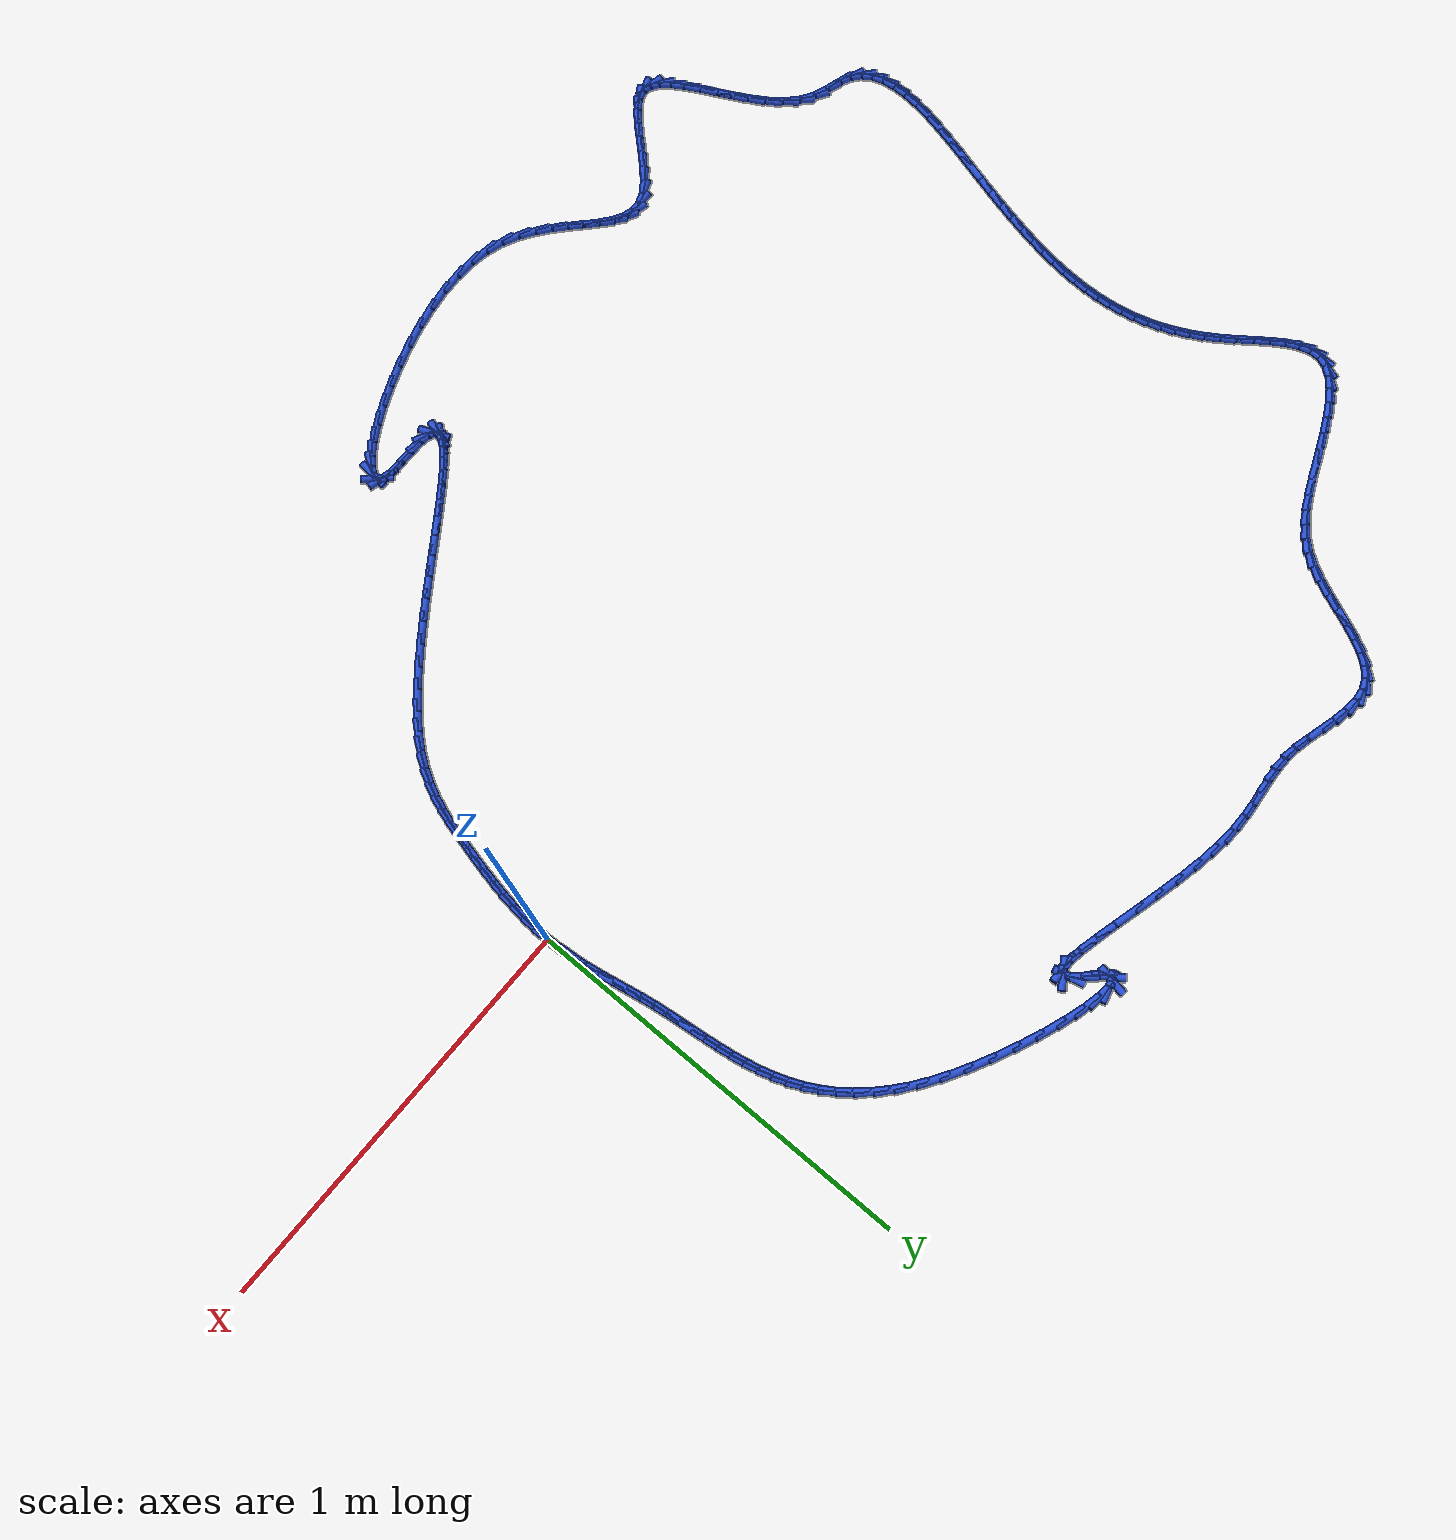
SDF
<sdf version="1.6">
 <world name="default">
  <light name="sun" type="directional">
   <pose>0 0 10 0 -0 0</pose>
   <diffuse>0.8 0.8 0.8 1</diffuse>
   <specular>0.2 0.2 0.2 1</specular>
   <attenuation>
    <range>1000</range>
    <constant>0.9</constant>
    <linear>0.01</linear>
    <quadratic>0.001</quadratic>
   </attenuation>
   <direction>-0.5 0.1 -0.9</direction>
  </light>
  <model name="ground_plane">
   <static>1</static>
   <link name="link">
    <collision name="collision">
     <geometry><plane><normal>0 0 1</normal><size>100 100</size></plane></geometry>
     <surface><friction><ode><mu>100</mu><mu2>50</mu2></ode></friction></surface>
    </collision>
    <visual name="visual">
     <cast_shadows>0</cast_shadows>
     <geometry><plane><normal>0 0 1</normal><size>100 100</size></plane></geometry>
     <material>
      <script><uri>file://media/materials/scripts/gazebo.material</uri><name>Gazebo/WhiteGlow</name></script>
     </material>
    </visual>
   </link>
  </model>
  <gravity>0 0 -9.8</gravity>
  <magnetic_field>6e-06 2.3e-05 -4.2e-05</magnetic_field>
  <atmosphere type="adiabatic"/>
  <physics name="default_physics" default="0" type="ode">
   <max_step_size>0.001</max_step_size>
   <real_time_factor>1</real_time_factor>
   <real_time_update_rate>1000</real_time_update_rate>
  </physics>
  <scene><ambient>0.4 0.4 0.4 1</ambient><background>0.7 0.7 0.7 1</background><shadows>1</shadows></scene>
  <spherical_coordinates>
   <surface_model>EARTH_WGS84</surface_model>
   <latitude_deg>0</latitude_deg>
   <longitude_deg>0</longitude_deg>
   <elevation>0</elevation>
   <heading_deg>0</heading_deg>
  </spherical_coordinates>
  <model name="line">
   <link name="link_0">
    <pose>1.0408340855860843e-17 2.0816681711721685e-17 0.01 0 1.57 -1.5239924957447901</pose>
    <collision name="collision">
     <geometry><cylinder><radius>0.01</radius><length>0.08</length></cylinder></geometry>
    </collision>
    <visual name="visual">
     <material>
      <script><name>Gazebo/Blue</name><uri>file://media/materials/scripts/gazebo.material</uri></script>
     </material>
     <geometry><cylinder><radius>0.01</radius><length>0.08</length></cylinder></geometry>
    </visual>
   </link>
   <link name="link_1">
    <pose>-0.001704649692244981 0.03639455868884389 0.01 0 1.57 -1.4743259532851969</pose>
    <collision name="collision">
     <geometry><cylinder><radius>0.01</radius><length>0.08</length></cylinder></geometry>
    </collision>
    <visual name="visual">
     <material>
      <script><name>Gazebo/Blue</name><uri>file://media/materials/scripts/gazebo.material</uri></script>
     </material>
     <geometry><cylinder><radius>0.01</radius><length>0.08</length></cylinder></geometry>
    </visual>
   </link>
   <link name="link_2">
    <pose>-0.005213107491138306 0.07264990894340112 0.01 0 1.57 -1.4358090419680396</pose>
    <collision name="collision">
     <geometry><cylinder><radius>0.01</radius><length>0.08</length></cylinder></geometry>
    </collision>
    <visual name="visual">
     <material>
      <script><name>Gazebo/Blue</name><uri>file://media/materials/scripts/gazebo.material</uri></script>
     </material>
     <geometry><cylinder><radius>0.01</radius><length>0.08</length></cylinder></geometry>
    </visual>
   </link>
   <link name="link_3">
    <pose>-0.01011653349412395 0.10875410249948468 0.01 0 1.57 -1.4083729899003963</pose>
    <collision name="collision">
     <geometry><cylinder><radius>0.01</radius><length>0.08</length></cylinder></geometry>
    </collision>
    <visual name="visual">
     <material>
      <script><name>Gazebo/Blue</name><uri>file://media/materials/scripts/gazebo.material</uri></script>
     </material>
     <geometry><cylinder><radius>0.01</radius><length>0.08</length></cylinder></geometry>
    </visual>
   </link>
   <link name="link_4">
    <pose>-0.016006087798645922 0.14469519109290768 0.01 0 1.57 -1.3919193030232373</pose>
    <collision name="collision">
     <geometry><cylinder><radius>0.01</radius><length>0.08</length></cylinder></geometry>
    </collision>
    <visual name="visual">
     <material>
      <script><name>Gazebo/Blue</name><uri>file://media/materials/scripts/gazebo.material</uri></script>
     </material>
     <geometry><cylinder><radius>0.01</radius><length>0.08</length></cylinder></geometry>
    </visual>
   </link>
   <link name="link_5">
    <pose>-0.022472930502148214 0.18046122645948304 0.01 0 1.57 -1.3864199840498364</pose>
    <collision name="collision">
     <geometry><cylinder><radius>0.01</radius><length>0.08</length></cylinder></geometry>
    </collision>
    <visual name="visual">
     <material>
      <script><name>Gazebo/Blue</name><uri>file://media/materials/scripts/gazebo.material</uri></script>
     </material>
     <geometry><cylinder><radius>0.01</radius><length>0.08</length></cylinder></geometry>
    </visual>
   </link>
   <link name="link_6">
    <pose>-0.029108221702074815 0.2160402603350239 0.01 0 1.57 -1.39197840082482</pose>
    <collision name="collision">
     <geometry><cylinder><radius>0.01</radius><length>0.08</length></cylinder></geometry>
    </collision>
    <visual name="visual">
     <material>
      <script><name>Gazebo/Blue</name><uri>file://media/materials/scripts/gazebo.material</uri></script>
     </material>
     <geometry><cylinder><radius>0.01</radius><length>0.08</length></cylinder></geometry>
    </visual>
   </link>
   <link name="link_7">
    <pose>-0.03550312149586973 0.25142034445534317 0.01 0 1.57 -1.4088456013283674</pose>
    <collision name="collision">
     <geometry><cylinder><radius>0.01</radius><length>0.08</length></cylinder></geometry>
    </collision>
    <visual name="visual">
     <material>
      <script><name>Gazebo/Blue</name><uri>file://media/materials/scripts/gazebo.material</uri></script>
     </material>
     <geometry><cylinder><radius>0.01</radius><length>0.08</length></cylinder></geometry>
    </visual>
   </link>
   <link name="link_8">
    <pose>-0.04124912028710268 0.286589531209608 0.01 0 1.57 -1.432309665168486</pose>
    <collision name="collision">
     <geometry><cylinder><radius>0.01</radius><length>0.08</length></cylinder></geometry>
    </collision>
    <visual name="visual">
     <material>
      <script><name>Gazebo/Blue</name><uri>file://media/materials/scripts/gazebo.material</uri></script>
     </material>
     <geometry><cylinder><radius>0.01</radius><length>0.08</length></cylinder></geometry>
    </visual>
   </link>
   <link name="link_9">
    <pose>-0.04611995080088553 0.32153623346692134 0.01 0 1.57 -1.448867968405959</pose>
    <collision name="collision">
     <geometry><cylinder><radius>0.01</radius><length>0.08</length></cylinder></geometry>
    </collision>
    <visual name="visual">
     <material>
      <script><name>Gazebo/Blue</name><uri>file://media/materials/scripts/gazebo.material</uri></script>
     </material>
     <geometry><cylinder><radius>0.01</radius><length>0.08</length></cylinder></geometry>
    </visual>
   </link>
   <link name="link_10">
    <pose>-0.05037362168738378 0.3562498220064544 0.01 0 1.57 -1.456012513739763</pose>
    <collision name="collision">
     <geometry><cylinder><radius>0.01</radius><length>0.08</length></cylinder></geometry>
    </collision>
    <visual name="visual">
     <material>
      <script><name>Gazebo/Blue</name><uri>file://media/materials/scripts/gazebo.material</uri></script>
     </material>
     <geometry><cylinder><radius>0.01</radius><length>0.08</length></cylinder></geometry>
    </visual>
   </link>
   <link name="link_11">
    <pose>-0.05434768861714777 0.3907198249534029 0.01 0 1.57 -1.4534969441290115</pose>
    <collision name="collision">
     <geometry><cylinder><radius>0.01</radius><length>0.08</length></cylinder></geometry>
    </collision>
    <visual name="visual">
     <material>
      <script><name>Gazebo/Blue</name><uri>file://media/materials/scripts/gazebo.material</uri></script>
     </material>
     <geometry><cylinder><radius>0.01</radius><length>0.08</length></cylinder></geometry>
    </visual>
   </link>
   <link name="link_12">
    <pose>-0.05837970726072789 0.4249357704329629 0.01 0 1.57 -1.4411204210888087</pose>
    <collision name="collision">
     <geometry><cylinder><radius>0.01</radius><length>0.08</length></cylinder></geometry>
    </collision>
    <visual name="visual">
     <material>
      <script><name>Gazebo/Blue</name><uri>file://media/materials/scripts/gazebo.material</uri></script>
     </material>
     <geometry><cylinder><radius>0.01</radius><length>0.08</length></cylinder></geometry>
    </visual>
   </link>
   <link name="link_13">
    <pose>-0.06280723328867449 0.4588871865703299 0.01 0 1.57 -1.4187387482534757</pose>
    <collision name="collision">
     <geometry><cylinder><radius>0.01</radius><length>0.08</length></cylinder></geometry>
    </collision>
    <visual name="visual">
     <material>
      <script><name>Gazebo/Blue</name><uri>file://media/materials/scripts/gazebo.material</uri></script>
     </material>
     <geometry><cylinder><radius>0.01</radius><length>0.08</length></cylinder></geometry>
    </visual>
   </link>
   <link name="link_14">
    <pose>-0.06796782237153794 0.49256360149069994 0.01 0 1.57 -1.3863046957361045</pose>
    <collision name="collision">
     <geometry><cylinder><radius>0.01</radius><length>0.08</length></cylinder></geometry>
    </collision>
    <visual name="visual">
     <material>
      <script><name>Gazebo/Blue</name><uri>file://media/materials/scripts/gazebo.material</uri></script>
     </material>
     <geometry><cylinder><radius>0.01</radius><length>0.08</length></cylinder></geometry>
    </visual>
   </link>
   <link name="link_15">
    <pose>-0.07419903017986862 0.5259545433192688 0.01 0 1.57 -1.3439379446227215</pose>
    <collision name="collision">
     <geometry><cylinder><radius>0.01</radius><length>0.08</length></cylinder></geometry>
    </collision>
    <visual name="visual">
     <material>
      <script><name>Gazebo/Blue</name><uri>file://media/materials/scripts/gazebo.material</uri></script>
     </material>
     <geometry><cylinder><radius>0.01</radius><length>0.08</length></cylinder></geometry>
    </visual>
   </link>
   <link name="link_16">
    <pose>-0.0818384123842169 0.5590495401812324 0.01 0 1.57 -1.2920188969965016</pose>
    <collision name="collision">
     <geometry><cylinder><radius>0.01</radius><length>0.08</length></cylinder></geometry>
    </collision>
    <visual name="visual">
     <material>
      <script><name>Gazebo/Blue</name><uri>file://media/materials/scripts/gazebo.material</uri></script>
     </material>
     <geometry><cylinder><radius>0.01</radius><length>0.08</length></cylinder></geometry>
    </visual>
   </link>
   <link name="link_17">
    <pose>-0.09122352465513311 0.5918381202017867 0.01 0 1.57 -1.231290097515232</pose>
    <collision name="collision">
     <geometry><cylinder><radius>0.01</radius><length>0.08</length></cylinder></geometry>
    </collision>
    <visual name="visual">
     <material>
      <script><name>Gazebo/Blue</name><uri>file://media/materials/scripts/gazebo.material</uri></script>
     </material>
     <geometry><cylinder><radius>0.01</radius><length>0.08</length></cylinder></geometry>
    </visual>
   </link>
   <link name="link_18">
    <pose>-0.10269192266316768 0.6243098115061271 0.01 0 1.57 -1.1629358616328311</pose>
    <collision name="collision">
     <geometry><cylinder><radius>0.01</radius><length>0.08</length></cylinder></geometry>
    </collision>
    <visual name="visual">
     <material>
      <script><name>Gazebo/Blue</name><uri>file://media/materials/scripts/gazebo.material</uri></script>
     </material>
     <geometry><cylinder><radius>0.01</radius><length>0.08</length></cylinder></geometry>
    </visual>
   </link>
   <link name="link_19">
    <pose>-0.1165811620788709 0.6564541422194498 0.01 0 1.57 -1.0886015923826649</pose>
    <collision name="collision">
     <geometry><cylinder><radius>0.01</radius><length>0.08</length></cylinder></geometry>
    </collision>
    <visual name="visual">
     <material>
      <script><name>Gazebo/Blue</name><uri>file://media/materials/scripts/gazebo.material</uri></script>
     </material>
     <geometry><cylinder><radius>0.01</radius><length>0.08</length></cylinder></geometry>
    </visual>
   </link>
   <link name="link_20">
    <pose>-0.1332287985727932 0.6882606404669505 0.01 0 1.57 -1.0103198007970067</pose>
    <collision name="collision">
     <geometry><cylinder><radius>0.01</radius><length>0.08</length></cylinder></geometry>
    </collision>
    <visual name="visual">
     <material>
      <script><name>Gazebo/Blue</name><uri>file://media/materials/scripts/gazebo.material</uri></script>
     </material>
     <geometry><cylinder><radius>0.01</radius><length>0.08</length></cylinder></geometry>
    </visual>
   </link>
   <link name="link_21">
    <pose>-0.15297238781548483 0.7197188343738248 0.01 0 1.57 -0.9303368503386841</pose>
    <collision name="collision">
     <geometry><cylinder><radius>0.01</radius><length>0.08</length></cylinder></geometry>
    </collision>
    <visual name="visual">
     <material>
      <script><name>Gazebo/Blue</name><uri>file://media/materials/scripts/gazebo.material</uri></script>
     </material>
     <geometry><cylinder><radius>0.01</radius><length>0.08</length></cylinder></geometry>
    </visual>
   </link>
   <link name="link_22">
    <pose>-0.17614948547749634 0.7508182520652689 0.01 0 1.57 -0.8508751186777291</pose>
    <collision name="collision">
     <geometry><cylinder><radius>0.01</radius><length>0.08</length></cylinder></geometry>
    </collision>
    <visual name="visual">
     <material>
      <script><name>Gazebo/Blue</name><uri>file://media/materials/scripts/gazebo.material</uri></script>
     </material>
     <geometry><cylinder><radius>0.01</radius><length>0.08</length></cylinder></geometry>
    </visual>
   </link>
   <link name="link_23">
    <pose>-0.203097647229378 0.7815484216664785 0.01 0 1.57 -0.7738962488050707</pose>
    <collision name="collision">
     <geometry><cylinder><radius>0.01</radius><length>0.08</length></cylinder></geometry>
    </collision>
    <visual name="visual">
     <material>
      <script><name>Gazebo/Blue</name><uri>file://media/materials/scripts/gazebo.material</uri></script>
     </material>
     <geometry><cylinder><radius>0.01</radius><length>0.08</length></cylinder></geometry>
    </visual>
   </link>
   <link name="link_24">
    <pose>-0.23415442874168024 0.8118988713026496 0.01 0 1.57 -0.7009307114150463</pose>
    <collision name="collision">
     <geometry><cylinder><radius>0.01</radius><length>0.08</length></cylinder></geometry>
    </collision>
    <visual name="visual">
     <material>
      <script><name>Gazebo/Blue</name><uri>file://media/materials/scripts/gazebo.material</uri></script>
     </material>
     <geometry><cylinder><radius>0.01</radius><length>0.08</length></cylinder></geometry>
    </visual>
   </link>
   <link name="link_25">
    <pose>-0.2696573856849533 0.8418591290989779 0.01 0 1.57 -0.6330074193401904</pose>
    <collision name="collision">
     <geometry><cylinder><radius>0.01</radius><length>0.08</length></cylinder></geometry>
    </collision>
    <visual name="visual">
     <material>
      <script><name>Gazebo/Blue</name><uri>file://media/materials/scripts/gazebo.material</uri></script>
     </material>
     <geometry><cylinder><radius>0.01</radius><length>0.08</length></cylinder></geometry>
    </visual>
   </link>
   <link name="link_26">
    <pose>-0.30994407372974764 0.8714187231806588 0.01 0 1.57 -0.5706808058501586</pose>
    <collision name="collision">
     <geometry><cylinder><radius>0.01</radius><length>0.08</length></cylinder></geometry>
    </collision>
    <visual name="visual">
     <material>
      <script><name>Gazebo/Blue</name><uri>file://media/materials/scripts/gazebo.material</uri></script>
     </material>
     <geometry><cylinder><radius>0.01</radius><length>0.08</length></cylinder></geometry>
    </visual>
   </link>
   <link name="link_27">
    <pose>-0.3553512412465966 0.9005669226028622 0.01 0 1.57 -0.5162154952429301</pose>
    <collision name="collision">
     <geometry><cylinder><radius>0.01</radius><length>0.08</length></cylinder></geometry>
    </collision>
    <visual name="visual">
     <material>
      <script><name>Gazebo/Blue</name><uri>file://media/materials/scripts/gazebo.material</uri></script>
     </material>
     <geometry><cylinder><radius>0.01</radius><length>0.08</length></cylinder></geometry>
    </visual>
   </link>
   <link name="link_28">
    <pose>-0.40564035361045087 0.9291083827975765 0.01 0 1.57 -0.4719669233111795</pose>
    <collision name="collision">
     <geometry><cylinder><radius>0.01</radius><length>0.08</length></cylinder></geometry>
    </collision>
    <visual name="visual">
     <material>
      <script><name>Gazebo/Blue</name><uri>file://media/materials/scripts/gazebo.material</uri></script>
     </material>
     <geometry><cylinder><radius>0.01</radius><length>0.08</length></cylinder></geometry>
    </visual>
   </link>
   <link name="link_29">
    <pose>-0.4589872181306473 0.9563389068878143 0.01 0 1.57 -0.43335633205329854</pose>
    <collision name="collision">
     <geometry><cylinder><radius>0.01</radius><length>0.08</length></cylinder></geometry>
    </collision>
    <visual name="visual">
     <material>
      <script><name>Gazebo/Blue</name><uri>file://media/materials/scripts/gazebo.material</uri></script>
     </material>
     <geometry><cylinder><radius>0.01</radius><length>0.08</length></cylinder></geometry>
    </visual>
   </link>
   <link name="link_30">
    <pose>-0.5132967834728371 0.9814673769577886 0.01 0 1.57 -0.39604228629437077</pose>
    <collision name="collision">
     <geometry><cylinder><radius>0.01</radius><length>0.08</length></cylinder></geometry>
    </collision>
    <visual name="visual">
     <material>
      <script><name>Gazebo/Blue</name><uri>file://media/materials/scripts/gazebo.material</uri></script>
     </material>
     <geometry><cylinder><radius>0.01</radius><length>0.08</length></cylinder></geometry>
    </visual>
   </link>
   <link name="link_31">
    <pose>-0.5664739983026715 1.0037026750917113 0.01 0 1.57 -0.3556045790316598</pose>
    <collision name="collision">
     <geometry><cylinder><radius>0.01</radius><length>0.08</length></cylinder></geometry>
    </collision>
    <visual name="visual">
     <material>
      <script><name>Gazebo/Blue</name><uri>file://media/materials/scripts/gazebo.material</uri></script>
     </material>
     <geometry><cylinder><radius>0.01</radius><length>0.08</length></cylinder></geometry>
    </visual>
   </link>
   <link name="link_32">
    <pose>-0.6164238112858011 1.0222536833737939 0.01 0 1.57 -0.30552735021120414</pose>
    <collision name="collision">
     <geometry><cylinder><radius>0.01</radius><length>0.08</length></cylinder></geometry>
    </collision>
    <visual name="visual">
     <material>
      <script><name>Gazebo/Blue</name><uri>file://media/materials/scripts/gazebo.material</uri></script>
     </material>
     <geometry><cylinder><radius>0.01</radius><length>0.08</length></cylinder></geometry>
    </visual>
   </link>
   <link name="link_33">
    <pose>-0.6610511710878771 1.0363292838882485 0.01 0 1.57 -0.23246060602367305</pose>
    <collision name="collision">
     <geometry><cylinder><radius>0.01</radius><length>0.08</length></cylinder></geometry>
    </collision>
    <visual name="visual">
     <material>
      <script><name>Gazebo/Blue</name><uri>file://media/materials/scripts/gazebo.material</uri></script>
     </material>
     <geometry><cylinder><radius>0.01</radius><length>0.08</length></cylinder></geometry>
    </visual>
   </link>
   <link name="link_34">
    <pose>-0.6982610263745507 1.0451383587192873 0.01 0 1.57 -0.09901448333140045</pose>
    <collision name="collision">
     <geometry><cylinder><radius>0.01</radius><length>0.08</length></cylinder></geometry>
    </collision>
    <visual name="visual">
     <material>
      <script><name>Gazebo/Blue</name><uri>file://media/materials/scripts/gazebo.material</uri></script>
     </material>
     <geometry><cylinder><radius>0.01</radius><length>0.08</length></cylinder></geometry>
    </visual>
   </link>
   <link name="link_35">
    <pose>-0.7259583258114729 1.0478897899511233 0.01 0 1.57 0.24935558453361537</pose>
    <collision name="collision">
     <geometry><cylinder><radius>0.01</radius><length>0.08</length></cylinder></geometry>
    </collision>
    <visual name="visual">
     <material>
      <script><name>Gazebo/Blue</name><uri>file://media/materials/scripts/gazebo.material</uri></script>
     </material>
     <geometry><cylinder><radius>0.01</radius><length>0.08</length></cylinder></geometry>
    </visual>
   </link>
   <link name="link_36">
    <pose>-0.7420480180642947 1.0437924596679675 0.01 0 1.57 1.3701594328385696</pose>
    <collision name="collision">
     <geometry><cylinder><radius>0.01</radius><length>0.08</length></cylinder></geometry>
    </collision>
    <visual name="visual">
     <material>
      <script><name>Gazebo/Blue</name><uri>file://media/materials/scripts/gazebo.material</uri></script>
     </material>
     <geometry><cylinder><radius>0.01</radius><length>0.08</length></cylinder></geometry>
    </visual>
   </link>
   <link name="link_37">
    <pose>-0.7444350517986671 1.0320552499540323 0.01 0 1.57 -0.984018469377502</pose>
    <collision name="collision">
     <geometry><cylinder><radius>0.01</radius><length>0.08</length></cylinder></geometry>
    </collision>
    <visual name="visual">
     <material>
      <script><name>Gazebo/Blue</name><uri>file://media/materials/scripts/gazebo.material</uri></script>
     </material>
     <geometry><cylinder><radius>0.01</radius><length>0.08</length></cylinder></geometry>
    </visual>
   </link>
   <link name="link_38">
    <pose>-0.7310256911333032 1.011887735739182 0.01 0 1.57 -0.7993445164497337</pose>
    <collision name="collision">
     <geometry><cylinder><radius>0.01</radius><length>0.08</length></cylinder></geometry>
    </collision>
    <visual name="visual">
     <material>
      <script><name>Gazebo/Blue</name><uri>file://media/materials/scripts/gazebo.material</uri></script>
     </material>
     <geometry><cylinder><radius>0.01</radius><length>0.08</length></cylinder></geometry>
    </visual>
   </link>
   <link name="link_39">
    <pose>-0.705301811926042 0.9854361519236258 0.01 0 1.57 -0.8819486344912955</pose>
    <collision name="collision">
     <geometry><cylinder><radius>0.01</radius><length>0.08</length></cylinder></geometry>
    </collision>
    <visual name="visual">
     <material>
      <script><name>Gazebo/Blue</name><uri>file://media/materials/scripts/gazebo.material</uri></script>
     </material>
     <geometry><cylinder><radius>0.01</radius><length>0.08</length></cylinder></geometry>
    </visual>
   </link>
   <link name="link_40">
    <pose>-0.6872418046976436 0.9635027153401807 0.01 0 1.57 -1.3406151099672403</pose>
    <collision name="collision">
     <geometry><cylinder><radius>0.01</radius><length>0.08</length></cylinder></geometry>
    </collision>
    <visual name="visual">
     <material>
      <script><name>Gazebo/Blue</name><uri>file://media/materials/scripts/gazebo.material</uri></script>
     </material>
     <geometry><cylinder><radius>0.01</radius><length>0.08</length></cylinder></geometry>
    </visual>
   </link>
   <link name="link_41">
    <pose>-0.6840455368372199 0.9498629501407568 0.01 0 1.57 0.5637328356442467</pose>
    <collision name="collision">
     <geometry><cylinder><radius>0.01</radius><length>0.08</length></cylinder></geometry>
    </collision>
    <visual name="visual">
     <material>
      <script><name>Gazebo/Blue</name><uri>file://media/materials/scripts/gazebo.material</uri></script>
     </material>
     <geometry><cylinder><radius>0.01</radius><length>0.08</length></cylinder></geometry>
    </visual>
   </link>
   <link name="link_42">
    <pose>-0.6941120176956872 0.9434993050487757 0.01 0 1.57 0.00691052210493459</pose>
    <collision name="collision">
     <geometry><cylinder><radius>0.01</radius><length>0.08</length></cylinder></geometry>
    </collision>
    <visual name="visual">
     <material>
      <script><name>Gazebo/Blue</name><uri>file://media/materials/scripts/gazebo.material</uri></script>
     </material>
     <geometry><cylinder><radius>0.01</radius><length>0.08</length></cylinder></geometry>
    </visual>
   </link>
   <link name="link_43">
    <pose>-0.7157585203674961 0.9433497140323046 0.01 0 1.57 -0.15727601696147575</pose>
    <collision name="collision">
     <geometry><cylinder><radius>0.01</radius><length>0.08</length></cylinder></geometry>
    </collision>
    <visual name="visual">
     <material>
      <script><name>Gazebo/Blue</name><uri>file://media/materials/scripts/gazebo.material</uri></script>
     </material>
     <geometry><cylinder><radius>0.01</radius><length>0.08</length></cylinder></geometry>
    </visual>
   </link>
   <link name="link_44">
    <pose>-0.7473023179470978 0.9483521110594113 0.01 0 1.57 -0.22482333381310624</pose>
    <collision name="collision">
     <geometry><cylinder><radius>0.01</radius><length>0.08</length></cylinder></geometry>
    </collision>
    <visual name="visual">
     <material>
      <script><name>Gazebo/Blue</name><uri>file://media/materials/scripts/gazebo.material</uri></script>
     </material>
     <geometry><cylinder><radius>0.01</radius><length>0.08</length></cylinder></geometry>
    </visual>
   </link>
   <link name="link_45">
    <pose>-0.7870606835289431 0.957444430098162 0.01 0 1.57 -0.2560816247083536</pose>
    <collision name="collision">
     <geometry><cylinder><radius>0.01</radius><length>0.08</length></cylinder></geometry>
    </collision>
    <visual name="visual">
     <material>
      <script><name>Gazebo/Blue</name><uri>file://media/materials/scripts/gazebo.material</uri></script>
     </material>
     <geometry><cylinder><radius>0.01</radius><length>0.08</length></cylinder></geometry>
    </visual>
   </link>
   <link name="link_46">
    <pose>-0.8333508902074833 0.9695646051166249 0.01 0 1.57 -0.2687779634327579</pose>
    <collision name="collision">
     <geometry><cylinder><radius>0.01</radius><length>0.08</length></cylinder></geometry>
    </collision>
    <visual name="visual">
     <material>
      <script><name>Gazebo/Blue</name><uri>file://media/materials/scripts/gazebo.material</uri></script>
     </material>
     <geometry><cylinder><radius>0.01</radius><length>0.08</length></cylinder></geometry>
    </visual>
   </link>
   <link name="link_47">
    <pose>-0.8844902110771694 0.9836505700828669 0.01 0 1.57 -0.2693181388148366</pose>
    <collision name="collision">
     <geometry><cylinder><radius>0.01</radius><length>0.08</length></cylinder></geometry>
    </collision>
    <visual name="visual">
     <material>
      <script><name>Gazebo/Blue</name><uri>file://media/materials/scripts/gazebo.material</uri></script>
     </material>
     <geometry><cylinder><radius>0.01</radius><length>0.08</length></cylinder></geometry>
    </visual>
   </link>
   <link name="link_48">
    <pose>-0.938795919232452 0.998640258964955 0.01 0 1.57 -0.25983548853780686</pose>
    <collision name="collision">
     <geometry><cylinder><radius>0.01</radius><length>0.08</length></cylinder></geometry>
    </collision>
    <visual name="visual">
     <material>
      <script><name>Gazebo/Blue</name><uri>file://media/materials/scripts/gazebo.material</uri></script>
     </material>
     <geometry><cylinder><radius>0.01</radius><length>0.08</length></cylinder></geometry>
    </visual>
   </link>
   <link name="link_49">
    <pose>-0.9945852877677822 1.0134716057309565 0.01 0 1.57 -0.24011987563167747</pose>
    <collision name="collision">
     <geometry><cylinder><radius>0.01</radius><length>0.08</length></cylinder></geometry>
    </collision>
    <visual name="visual">
     <material>
      <script><name>Gazebo/Blue</name><uri>file://media/materials/scripts/gazebo.material</uri></script>
     </material>
     <geometry><cylinder><radius>0.01</radius><length>0.08</length></cylinder></geometry>
    </visual>
   </link>
   <link name="link_50">
    <pose>-1.050175589777611 1.0270825443489389 0.01 0 1.57 -0.20787791092671823</pose>
    <collision name="collision">
     <geometry><cylinder><radius>0.01</radius><length>0.08</length></cylinder></geometry>
    </collision>
    <visual name="visual">
     <material>
      <script><name>Gazebo/Blue</name><uri>file://media/materials/scripts/gazebo.material</uri></script>
     </material>
     <geometry><cylinder><radius>0.01</radius><length>0.08</length></cylinder></geometry>
    </visual>
   </link>
   <link name="link_51">
    <pose>-1.1038840983563896 1.0384110087869691 0.01 0 1.57 -0.15789460859083612</pose>
    <collision name="collision">
     <geometry><cylinder><radius>0.01</radius><length>0.08</length></cylinder></geometry>
    </collision>
    <visual name="visual">
     <material>
      <script><name>Gazebo/Blue</name><uri>file://media/materials/scripts/gazebo.material</uri></script>
     </material>
     <geometry><cylinder><radius>0.01</radius><length>0.08</length></cylinder></geometry>
    </visual>
   </link>
   <link name="link_52">
    <pose>-1.1540280865985686 1.0463949330131146 0.01 0 1.57 -0.08477968536149154</pose>
    <collision name="collision">
     <geometry><cylinder><radius>0.01</radius><length>0.08</length></cylinder></geometry>
    </collision>
    <visual name="visual">
     <material>
      <script><name>Gazebo/Blue</name><uri>file://media/materials/scripts/gazebo.material</uri></script>
     </material>
     <geometry><cylinder><radius>0.01</radius><length>0.08</length></cylinder></geometry>
    </visual>
   </link>
   <link name="link_53">
    <pose>-1.199242314472679 1.0502373914521907 0.01 0 1.57 -0.009186519523485804</pose>
    <collision name="collision">
     <geometry><cylinder><radius>0.01</radius><length>0.08</length></cylinder></geometry>
    </collision>
    <visual name="visual">
     <material>
      <script><name>Gazebo/Blue</name><uri>file://media/materials/scripts/gazebo.material</uri></script>
     </material>
     <geometry><cylinder><radius>0.01</radius><length>0.08</length></cylinder></geometry>
    </visual>
   </link>
   <link name="link_54">
    <pose>-1.2399213339603703 1.050611100571674 0.01 0 1.57 0.05153656360541167</pose>
    <collision name="collision">
     <geometry><cylinder><radius>0.01</radius><length>0.08</length></cylinder></geometry>
    </collision>
    <visual name="visual">
     <material>
      <script><name>Gazebo/Blue</name><uri>file://media/materials/scripts/gazebo.material</uri></script>
     </material>
     <geometry><cylinder><radius>0.01</radius><length>0.08</length></cylinder></geometry>
    </visual>
   </link>
   <link name="link_55">
    <pose>-1.2770659790074037 1.0486950965958768 0.01 0 1.57 0.0872114523953904</pose>
    <collision name="collision">
     <geometry><cylinder><radius>0.01</radius><length>0.08</length></cylinder></geometry>
    </collision>
    <visual name="visual">
     <material>
      <script><name>Gazebo/Blue</name><uri>file://media/materials/scripts/gazebo.material</uri></script>
     </material>
     <geometry><cylinder><radius>0.01</radius><length>0.08</length></cylinder></geometry>
    </visual>
   </link>
   <link name="link_56">
    <pose>-1.3116776473134988 1.0456688865527721 0.01 0 1.57 0.089149440896652</pose>
    <collision name="collision">
     <geometry><cylinder><radius>0.01</radius><length>0.08</length></cylinder></geometry>
    </collision>
    <visual name="visual">
     <material>
      <script><name>Gazebo/Blue</name><uri>file://media/materials/scripts/gazebo.material</uri></script>
     </material>
     <geometry><cylinder><radius>0.01</radius><length>0.08</length></cylinder></geometry>
    </visual>
   </link>
   <link name="link_57">
    <pose>-1.3447577365783774 1.0427119774703315 0.01 0 1.57 0.05242828267476847</pose>
    <collision name="collision">
     <geometry><cylinder><radius>0.01</radius><length>0.08</length></cylinder></geometry>
    </collision>
    <visual name="visual">
     <material>
      <script><name>Gazebo/Blue</name><uri>file://media/materials/scripts/gazebo.material</uri></script>
     </material>
     <geometry><cylinder><radius>0.01</radius><length>0.08</length></cylinder></geometry>
    </visual>
   </link>
   <link name="link_58">
    <pose>-1.3773076445017587 1.041003876376529 0.01 0 1.57 -0.02180724513530175</pose>
    <collision name="collision">
     <geometry><cylinder><radius>0.01</radius><length>0.08</length></cylinder></geometry>
    </collision>
    <visual name="visual">
     <material>
      <script><name>Gazebo/Blue</name><uri>file://media/materials/scripts/gazebo.material</uri></script>
     </material>
     <geometry><cylinder><radius>0.01</radius><length>0.08</length></cylinder></geometry>
    </visual>
   </link>
   <link name="link_59">
    <pose>-1.4103287687833657 1.0417240902993374 0.01 0 1.57 -0.12481042961064903</pose>
    <collision name="collision">
     <geometry><cylinder><radius>0.01</radius><length>0.08</length></cylinder></geometry>
    </collision>
    <visual name="visual">
     <material>
      <script><name>Gazebo/Blue</name><uri>file://media/materials/scripts/gazebo.material</uri></script>
     </material>
     <geometry><cylinder><radius>0.01</radius><length>0.08</length></cylinder></geometry>
    </visual>
   </link>
   <link name="link_60">
    <pose>-1.4448222674865456 1.0460517335571842 0.01 0 1.57 -0.2255673482702717</pose>
    <collision name="collision">
     <geometry><cylinder><radius>0.01</radius><length>0.08</length></cylinder></geometry>
    </collision>
    <visual name="visual">
     <material>
      <script><name>Gazebo/Blue</name><uri>file://media/materials/scripts/gazebo.material</uri></script>
     </material>
     <geometry><cylinder><radius>0.01</radius><length>0.08</length></cylinder></geometry>
    </visual>
   </link>
   <link name="link_61">
    <pose>-1.481341367666463 1.054431863358171 0.01 0 1.57 -0.27444721846377584</pose>
    <collision name="collision">
     <geometry><cylinder><radius>0.01</radius><length>0.08</length></cylinder></geometry>
    </collision>
    <visual name="visual">
     <material>
      <script><name>Gazebo/Blue</name><uri>file://media/materials/scripts/gazebo.material</uri></script>
     </material>
     <geometry><cylinder><radius>0.01</radius><length>0.08</length></cylinder></geometry>
    </visual>
   </link>
   <link name="link_62">
    <pose>-1.5190617927091894 1.0650521214952655 0.01 0 1.57 -0.27355057682879086</pose>
    <collision name="collision">
     <geometry><cylinder><radius>0.01</radius><length>0.08</length></cylinder></geometry>
    </collision>
    <visual name="visual">
     <material>
      <script><name>Gazebo/Blue</name><uri>file://media/materials/scripts/gazebo.material</uri></script>
     </material>
     <geometry><cylinder><radius>0.01</radius><length>0.08</length></cylinder></geometry>
    </visual>
   </link>
   <link name="link_63">
    <pose>-1.5568953336264255 1.0756676245901169 0.01 0 1.57 -0.2231913755646232</pose>
    <collision name="collision">
     <geometry><cylinder><radius>0.01</radius><length>0.08</length></cylinder></geometry>
    </collision>
    <visual name="visual">
     <material>
      <script><name>Gazebo/Blue</name><uri>file://media/materials/scripts/gazebo.material</uri></script>
     </material>
     <geometry><cylinder><radius>0.01</radius><length>0.08</length></cylinder></geometry>
    </visual>
   </link>
   <link name="link_64">
    <pose>-1.5937537814298677 1.0840334892643733 0.01 0 1.57 -0.11080528452260247</pose>
    <collision name="collision">
     <geometry><cylinder><radius>0.01</radius><length>0.08</length></cylinder></geometry>
    </collision>
    <visual name="visual">
     <material>
      <script><name>Gazebo/Blue</name><uri>file://media/materials/scripts/gazebo.material</uri></script>
     </material>
     <geometry><cylinder><radius>0.01</radius><length>0.08</length></cylinder></geometry>
    </visual>
   </link>
   <link name="link_65">
    <pose>-1.628548927131216 1.0879048321396847 0.01 0 1.57 0.09038933636369866</pose>
    <collision name="collision">
     <geometry><cylinder><radius>0.01</radius><length>0.08</length></cylinder></geometry>
    </collision>
    <visual name="visual">
     <material>
      <script><name>Gazebo/Blue</name><uri>file://media/materials/scripts/gazebo.material</uri></script>
     </material>
     <geometry><cylinder><radius>0.01</radius><length>0.08</length></cylinder></geometry>
    </visual>
   </link>
   <link name="link_66">
    <pose>-1.6601925617421696 1.0850367698376995 0.01 0 1.57 0.3955872255324894</pose>
    <collision name="collision">
     <geometry><cylinder><radius>0.01</radius><length>0.08</length></cylinder></geometry>
    </collision>
    <visual name="visual">
     <material>
      <script><name>Gazebo/Blue</name><uri>file://media/materials/scripts/gazebo.material</uri></script>
     </material>
     <geometry><cylinder><radius>0.01</radius><length>0.08</length></cylinder></geometry>
    </visual>
   </link>
   <link name="link_67">
    <pose>-1.6877645495275815 1.0735226720178574 0.01 0 1.57 0.6913963453238366</pose>
    <collision name="collision">
     <geometry><cylinder><radius>0.01</radius><length>0.08</length></cylinder></geometry>
    </collision>
    <visual name="visual">
     <material>
      <script><name>Gazebo/Blue</name><uri>file://media/materials/scripts/gazebo.material</uri></script>
     </material>
     <geometry><cylinder><radius>0.01</radius><length>0.08</length></cylinder></geometry>
    </visual>
   </link>
   <link name="link_68">
    <pose>-1.71153390100302 1.0538491049019865 0.01 0 1.57 0.903109626143905</pose>
    <collision name="collision">
     <geometry><cylinder><radius>0.01</radius><length>0.08</length></cylinder></geometry>
    </collision>
    <visual name="visual">
     <material>
      <script><name>Gazebo/Blue</name><uri>file://media/materials/scripts/gazebo.material</uri></script>
     </material>
     <geometry><cylinder><radius>0.01</radius><length>0.08</length></cylinder></geometry>
    </visual>
   </link>
   <link name="link_69">
    <pose>-1.7322825432388422 1.027534896416462 0.01 0 1.57 1.0385407945591603</pose>
    <collision name="collision">
     <geometry><cylinder><radius>0.01</radius><length>0.08</length></cylinder></geometry>
    </collision>
    <visual name="visual">
     <material>
      <script><name>Gazebo/Blue</name><uri>file://media/materials/scripts/gazebo.material</uri></script>
     </material>
     <geometry><cylinder><radius>0.01</radius><length>0.08</length></cylinder></geometry>
    </visual>
   </link>
   <link name="link_70">
    <pose>-1.750794422602795 0.9961029383911211 0.01 0 1.57 1.1175795403811848</pose>
    <collision name="collision">
     <geometry><cylinder><radius>0.01</radius><length>0.08</length></cylinder></geometry>
    </collision>
    <visual name="visual">
     <material>
      <script><name>Gazebo/Blue</name><uri>file://media/materials/scripts/gazebo.material</uri></script>
     </material>
     <geometry><cylinder><radius>0.01</radius><length>0.08</length></cylinder></geometry>
    </visual>
   </link>
   <link name="link_71">
    <pose>-1.767853485462622 0.9610761226558012 0.01 0 1.57 1.1547835154055661</pose>
    <collision name="collision">
     <geometry><cylinder><radius>0.01</radius><length>0.08</length></cylinder></geometry>
    </collision>
    <visual name="visual">
     <material>
      <script><name>Gazebo/Blue</name><uri>file://media/materials/scripts/gazebo.material</uri></script>
     </material>
     <geometry><cylinder><radius>0.01</radius><length>0.08</length></cylinder></geometry>
    </visual>
   </link>
   <link name="link_72">
    <pose>-1.7842436781860682 0.9239773410403385 0.01 0 1.57 1.157620720772946</pose>
    <collision name="collision">
     <geometry><cylinder><radius>0.01</radius><length>0.08</length></cylinder></geometry>
    </collision>
    <visual name="visual">
     <material>
      <script><name>Gazebo/Blue</name><uri>file://media/materials/scripts/gazebo.material</uri></script>
     </material>
     <geometry><cylinder><radius>0.01</radius><length>0.08</length></cylinder></geometry>
    </visual>
   </link>
   <link name="link_73">
    <pose>-1.8007489471408802 0.8863294853745715 0.01 0 1.57 1.127701262763376</pose>
    <collision name="collision">
     <geometry><cylinder><radius>0.01</radius><length>0.08</length></cylinder></geometry>
    </collision>
    <visual name="visual">
     <material>
      <script><name>Gazebo/Blue</name><uri>file://media/materials/scripts/gazebo.material</uri></script>
     </material>
     <geometry><cylinder><radius>0.01</radius><length>0.08</length></cylinder></geometry>
    </visual>
   </link>
   <link name="link_74">
    <pose>-1.8181532386948018 0.8496554474883358 0.01 0 1.57 1.0614679715722342</pose>
    <collision name="collision">
     <geometry><cylinder><radius>0.01</radius><length>0.08</length></cylinder></geometry>
    </collision>
    <visual name="visual">
     <material>
      <script><name>Gazebo/Blue</name><uri>file://media/materials/scripts/gazebo.material</uri></script>
     </material>
     <geometry><cylinder><radius>0.01</radius><length>0.08</length></cylinder></geometry>
    </visual>
   </link>
   <link name="link_75">
    <pose>-1.837240499215578 0.8154781192114696 0.01 0 1.57 0.9508166535194016</pose>
    <collision name="collision">
     <geometry><cylinder><radius>0.01</radius><length>0.08</length></cylinder></geometry>
    </collision>
    <visual name="visual">
     <material>
      <script><name>Gazebo/Blue</name><uri>file://media/materials/scripts/gazebo.material</uri></script>
     </material>
     <geometry><cylinder><radius>0.01</radius><length>0.08</length></cylinder></geometry>
    </visual>
   </link>
   <link name="link_76">
    <pose>-1.8587872111108235 0.7852955078681247 0.01 0 1.57 0.8097696549413556</pose>
    <collision name="collision">
     <geometry><cylinder><radius>0.01</radius><length>0.08</length></cylinder></geometry>
    </collision>
    <visual name="visual">
     <material>
      <script><name>Gazebo/Blue</name><uri>file://media/materials/scripts/gazebo.material</uri></script>
     </material>
     <geometry><cylinder><radius>0.01</radius><length>0.08</length></cylinder></geometry>
    </visual>
   </link>
   <link name="link_77">
    <pose>-1.883266209819236 0.7595932755137452 0.01 0 1.57 0.6767906121939151</pose>
    <collision name="collision">
     <geometry><cylinder><radius>0.01</radius><length>0.08</length></cylinder></geometry>
    </collision>
    <visual name="visual">
     <material>
      <script><name>Gazebo/Blue</name><uri>file://media/materials/scripts/gazebo.material</uri></script>
     </material>
     <geometry><cylinder><radius>0.01</radius><length>0.08</length></cylinder></geometry>
    </visual>
   </link>
   <link name="link_78">
    <pose>-1.9107478987359694 0.7375153939616118 0.01 0 1.57 0.5661609985635575</pose>
    <collision name="collision">
     <geometry><cylinder><radius>0.01</radius><length>0.08</length></cylinder></geometry>
    </collision>
    <visual name="visual">
     <material>
      <script><name>Gazebo/Blue</name><uri>file://media/materials/scripts/gazebo.material</uri></script>
     </material>
     <geometry><cylinder><radius>0.01</radius><length>0.08</length></cylinder></geometry>
    </visual>
   </link>
   <link name="link_79">
    <pose>-1.941274967638765 0.7181134390772858 0.01 0 1.57 0.48406490635298116</pose>
    <collision name="collision">
     <geometry><cylinder><radius>0.01</radius><length>0.08</length></cylinder></geometry>
    </collision>
    <visual name="visual">
     <material>
      <script><name>Gazebo/Blue</name><uri>file://media/materials/scripts/gazebo.material</uri></script>
     </material>
     <geometry><cylinder><radius>0.01</radius><length>0.08</length></cylinder></geometry>
    </visual>
   </link>
   <link name="link_80">
    <pose>-1.9748901063053654 0.7004389867263263 0.01 0 1.57 0.4309516659975358</pose>
    <collision name="collision">
     <geometry><cylinder><radius>0.01</radius><length>0.08</length></cylinder></geometry>
    </collision>
    <visual name="visual">
     <material>
      <script><name>Gazebo/Blue</name><uri>file://media/materials/scripts/gazebo.material</uri></script>
     </material>
     <geometry><cylinder><radius>0.01</radius><length>0.08</length></cylinder></geometry>
    </visual>
   </link>
   <link name="link_81">
    <pose>-2.0116087986780204 0.6835567101678456 0.01 0 1.57 0.4030996805885406</pose>
    <collision name="collision">
     <geometry><cylinder><radius>0.01</radius><length>0.08</length></cylinder></geometry>
    </collision>
    <visual name="visual">
     <material>
      <script><name>Gazebo/Blue</name><uri>file://media/materials/scripts/gazebo.material</uri></script>
     </material>
     <geometry><cylinder><radius>0.01</radius><length>0.08</length></cylinder></geometry>
    </visual>
   </link>
   <link name="link_82">
    <pose>-2.0507814652660357 0.6668514565266183 0.01 0 1.57 0.39532140853153785</pose>
    <collision name="collision">
     <geometry><cylinder><radius>0.01</radius><length>0.08</length></cylinder></geometry>
    </collision>
    <visual name="visual">
     <material>
      <script><name>Gazebo/Blue</name><uri>file://media/materials/scripts/gazebo.material</uri></script>
     </material>
     <geometry><cylinder><radius>0.01</radius><length>0.08</length></cylinder></geometry>
    </visual>
   </link>
   <link name="link_83">
    <pose>-2.091070850795724 0.6500391327975827 0.01 0 1.57 0.40551296501582323</pose>
    <collision name="collision">
     <geometry><cylinder><radius>0.01</radius><length>0.08</length></cylinder></geometry>
    </collision>
    <visual name="visual">
     <material>
      <script><name>Gazebo/Blue</name><uri>file://media/materials/scripts/gazebo.material</uri></script>
     </material>
     <geometry><cylinder><radius>0.01</radius><length>0.08</length></cylinder></geometry>
    </visual>
   </link>
   <link name="link_84">
    <pose>-2.131107970102979 0.6328509213331404 0.01 0 1.57 0.43460550154439176</pose>
    <collision name="collision">
     <geometry><cylinder><radius>0.01</radius><length>0.08</length></cylinder></geometry>
    </collision>
    <visual name="visual">
     <material>
      <script><name>Gazebo/Blue</name><uri>file://media/materials/scripts/gazebo.material</uri></script>
     </material>
     <geometry><cylinder><radius>0.01</radius><length>0.08</length></cylinder></geometry>
    </visual>
   </link>
   <link name="link_85">
    <pose>-2.169523838023697 0.6150180044856917 0.01 0 1.57 0.48671607632007813</pose>
    <collision name="collision">
     <geometry><cylinder><radius>0.01</radius><length>0.08</length></cylinder></geometry>
    </collision>
    <visual name="visual">
     <material>
      <script><name>Gazebo/Blue</name><uri>file://media/materials/scripts/gazebo.material</uri></script>
     </material>
     <geometry><cylinder><radius>0.01</radius><length>0.08</length></cylinder></geometry>
    </visual>
   </link>
   <link name="link_86">
    <pose>-2.2049494693937723 0.5962715646076375 0.01 0 1.57 0.570369272431806</pose>
    <collision name="collision">
     <geometry><cylinder><radius>0.01</radius><length>0.08</length></cylinder></geometry>
    </collision>
    <visual name="visual">
     <material>
      <script><name>Gazebo/Blue</name><uri>file://media/materials/scripts/gazebo.material</uri></script>
     </material>
     <geometry><cylinder><radius>0.01</radius><length>0.08</length></cylinder></geometry>
    </visual>
   </link>
   <link name="link_87">
    <pose>-2.236015879049099 0.5763427840513783 0.01 0 1.57 0.7008735488887303</pose>
    <collision name="collision">
     <geometry><cylinder><radius>0.01</radius><length>0.08</length></cylinder></geometry>
    </collision>
    <visual name="visual">
     <material>
      <script><name>Gazebo/Blue</name><uri>file://media/materials/scripts/gazebo.material</uri></script>
     </material>
     <geometry><cylinder><radius>0.01</radius><length>0.08</length></cylinder></geometry>
    </visual>
   </link>
   <link name="link_88">
    <pose>-2.2613540818255706 0.5549628451693154 0.01 0 1.57 0.9023939541753669</pose>
    <collision name="collision">
     <geometry><cylinder><radius>0.01</radius><length>0.08</length></cylinder></geometry>
    </collision>
    <visual name="visual">
     <material>
      <script><name>Gazebo/Blue</name><uri>file://media/materials/scripts/gazebo.material</uri></script>
     </material>
     <geometry><cylinder><radius>0.01</radius><length>0.08</length></cylinder></geometry>
    </visual>
   </link>
   <link name="link_89">
    <pose>-2.2795950925590827 0.5318629303138487 0.01 0 1.57 1.1992780549242128</pose>
    <collision name="collision">
     <geometry><cylinder><radius>0.01</radius><length>0.08</length></cylinder></geometry>
    </collision>
    <visual name="visual">
     <material>
      <script><name>Gazebo/Blue</name><uri>file://media/materials/scripts/gazebo.material</uri></script>
     </material>
     <geometry><cylinder><radius>0.01</radius><length>0.08</length></cylinder></geometry>
    </visual>
   </link>
   <link name="link_90">
    <pose>-2.2893699260855294 0.5067742218373799 0.01 0 1.57 1.5658764252955046</pose>
    <collision name="collision">
     <geometry><cylinder><radius>0.01</radius><length>0.08</length></cylinder></geometry>
    </collision>
    <visual name="visual">
     <material>
      <script><name>Gazebo/Blue</name><uri>file://media/materials/scripts/gazebo.material</uri></script>
     </material>
     <geometry><cylinder><radius>0.01</radius><length>0.08</length></cylinder></geometry>
    </visual>
   </link>
   <link name="link_91">
    <pose>-2.289504278223832 0.4794665502711252 0.01 0 1.57 -1.2825446229990702</pose>
    <collision name="collision">
     <geometry><cylinder><radius>0.01</radius><length>0.08</length></cylinder></geometry>
    </collision>
    <visual name="visual">
     <material>
      <script><name>Gazebo/Blue</name><uri>file://media/materials/scripts/gazebo.material</uri></script>
     </material>
     <geometry><cylinder><radius>0.01</radius><length>0.08</length></cylinder></geometry>
    </visual>
   </link>
   <link name="link_92">
    <pose>-2.2807972557975162 0.450101508814637 0.01 0 1.57 -1.1049607791867386</pose>
    <collision name="collision">
     <geometry><cylinder><radius>0.01</radius><length>0.08</length></cylinder></geometry>
    </collision>
    <visual name="visual">
     <material>
      <script><name>Gazebo/Blue</name><uri>file://media/materials/scripts/gazebo.material</uri></script>
     </material>
     <geometry><cylinder><radius>0.01</radius><length>0.08</length></cylinder></geometry>
    </visual>
   </link>
   <link name="link_93">
    <pose>-2.2651958169598725 0.4190685627624063 0.01 0 1.57 -1.0046249370908606</pose>
    <collision name="collision">
     <geometry><cylinder><radius>0.01</radius><length>0.08</length></cylinder></geometry>
    </collision>
    <visual name="visual">
     <material>
      <script><name>Gazebo/Blue</name><uri>file://media/materials/scripts/gazebo.material</uri></script>
     </material>
     <geometry><cylinder><radius>0.01</radius><length>0.08</length></cylinder></geometry>
    </visual>
   </link>
   <link name="link_94">
    <pose>-2.2446611340201894 0.3867599992112114 0.01 0 1.57 -0.9545830559526337</pose>
    <collision name="collision">
     <geometry><cylinder><radius>0.01</radius><length>0.08</length></cylinder></geometry>
    </collision>
    <visual name="visual">
     <material>
      <script><name>Gazebo/Blue</name><uri>file://media/materials/scripts/gazebo.material</uri></script>
     </material>
     <geometry><cylinder><radius>0.01</radius><length>0.08</length></cylinder></geometry>
    </visual>
   </link>
   <link name="link_95">
    <pose>-2.221154379287756 0.353568105257829 0.01 0 1.57 -0.9415929163186542</pose>
    <collision name="collision">
     <geometry><cylinder><radius>0.01</radius><length>0.08</length></cylinder></geometry>
    </collision>
    <visual name="visual">
     <material>
      <script><name>Gazebo/Blue</name><uri>file://media/materials/scripts/gazebo.material</uri></script>
     </material>
     <geometry><cylinder><radius>0.01</radius><length>0.08</length></cylinder></geometry>
    </visual>
   </link>
   <link name="link_96">
    <pose>-2.196636725071864 0.3198851679990372 0.01 0 1.57 -0.9616553987253521</pose>
    <collision name="collision">
     <geometry><cylinder><radius>0.01</radius><length>0.08</length></cylinder></geometry>
    </collision>
    <visual name="visual">
     <material>
      <script><name>Gazebo/Blue</name><uri>file://media/materials/scripts/gazebo.material</uri></script>
     </material>
     <geometry><cylinder><radius>0.01</radius><length>0.08</length></cylinder></geometry>
    </visual>
   </link>
   <link name="link_97">
    <pose>-2.1730692131092937 0.2861034450836528 0.01 0 1.57 -1.0102687768695662</pose>
    <collision name="collision">
     <geometry><cylinder><radius>0.01</radius><length>0.08</length></cylinder></geometry>
    </collision>
    <visual name="visual">
     <material>
      <script><name>Gazebo/Blue</name><uri>file://media/materials/scripts/gazebo.material</uri></script>
     </material>
     <geometry><cylinder><radius>0.01</radius><length>0.08</length></cylinder></geometry>
    </visual>
   </link>
   <link name="link_98">
    <pose>-2.1519891688113115 0.25251963360276775 0.01 0 1.57 -1.066751540448809</pose>
    <collision name="collision">
     <geometry><cylinder><radius>0.01</radius><length>0.08</length></cylinder></geometry>
    </collision>
    <visual name="visual">
     <material>
      <script><name>Gazebo/Blue</name><uri>file://media/materials/scripts/gazebo.material</uri></script>
     </material>
     <geometry><cylinder><radius>0.01</radius><length>0.08</length></cylinder></geometry>
    </visual>
   </link>
   <link name="link_99">
    <pose>-2.1335684271473987 0.21912247218487627 0.01 0 1.57 -1.1260154734263697</pose>
    <collision name="collision">
     <geometry><cylinder><radius>0.01</radius><length>0.08</length></cylinder></geometry>
    </collision>
    <visual name="visual">
     <material>
      <script><name>Gazebo/Blue</name><uri>file://media/materials/scripts/gazebo.material</uri></script>
     </material>
     <geometry><cylinder><radius>0.01</radius><length>0.08</length></cylinder></geometry>
    </visual>
   </link>
   <link name="link_100">
    <pose>-2.117704282237479 0.1858387823806481 0.01 0 1.57 -1.187365775276839</pose>
    <collision name="collision">
     <geometry><cylinder><radius>0.01</radius><length>0.08</length></cylinder></geometry>
    </collision>
    <visual name="visual">
     <material>
      <script><name>Gazebo/Blue</name><uri>file://media/materials/scripts/gazebo.material</uri></script>
     </material>
     <geometry><cylinder><radius>0.01</radius><length>0.08</length></cylinder></geometry>
    </visual>
   </link>
   <link name="link_101">
    <pose>-2.1042940282014766 0.15259538574075468 0.01 0 1.57 -1.2499392401147815</pose>
    <collision name="collision">
     <geometry><cylinder><radius>0.01</radius><length>0.08</length></cylinder></geometry>
    </collision>
    <visual name="visual">
     <material>
      <script><name>Gazebo/Blue</name><uri>file://media/materials/scripts/gazebo.material</uri></script>
     </material>
     <geometry><cylinder><radius>0.01</radius><length>0.08</length></cylinder></geometry>
    </visual>
   </link>
   <link name="link_102">
    <pose>-2.0932349591593153 0.11931910381586579 0.01 0 1.57 -1.3127510024799658</pose>
    <collision name="collision">
     <geometry><cylinder><radius>0.01</radius><length>0.08</length></cylinder></geometry>
    </collision>
    <visual name="visual">
     <material>
      <script><name>Gazebo/Blue</name><uri>file://media/materials/scripts/gazebo.material</uri></script>
     </material>
     <geometry><cylinder><radius>0.01</radius><length>0.08</length></cylinder></geometry>
    </visual>
   </link>
   <link name="link_103">
    <pose>-2.0844243692309203 0.08593675815665282 0.01 0 1.57 -1.3747620351923138</pose>
    <collision name="collision">
     <geometry><cylinder><radius>0.01</radius><length>0.08</length></cylinder></geometry>
    </collision>
    <visual name="visual">
     <material>
      <script><name>Gazebo/Blue</name><uri>file://media/materials/scripts/gazebo.material</uri></script>
     </material>
     <geometry><cylinder><radius>0.01</radius><length>0.08</length></cylinder></geometry>
    </visual>
   </link>
   <link name="link_104">
    <pose>-2.077759552536215 0.05237517031378556 0.01 0 1.57 -1.4349565669418225</pose>
    <collision name="collision">
     <geometry><cylinder><radius>0.01</radius><length>0.08</length></cylinder></geometry>
    </collision>
    <visual name="visual">
     <material>
      <script><name>Gazebo/Blue</name><uri>file://media/materials/scripts/gazebo.material</uri></script>
     </material>
     <geometry><cylinder><radius>0.01</radius><length>0.08</length></cylinder></geometry>
    </visual>
   </link>
   <link name="link_105">
    <pose>-2.0731378031951233 0.01856116183793545 0.01 0 1.57 -1.4924153872030097</pose>
    <collision name="collision">
     <geometry><cylinder><radius>0.01</radius><length>0.08</length></cylinder></geometry>
    </collision>
    <visual name="visual">
     <material>
      <script><name>Gazebo/Blue</name><uri>file://media/materials/scripts/gazebo.material</uri></script>
     </material>
     <geometry><cylinder><radius>0.01</radius><length>0.08</length></cylinder></geometry>
    </visual>
   </link>
   <link name="link_106">
    <pose>-2.0704564153275697 -0.015578445720227749 0.01 0 1.57 -1.5463723563459548</pose>
    <collision name="collision">
     <geometry><cylinder><radius>0.01</radius><length>0.08</length></cylinder></geometry>
    </collision>
    <visual name="visual">
     <material>
      <script><name>Gazebo/Blue</name><uri>file://media/materials/scripts/gazebo.material</uri></script>
     </material>
     <geometry><cylinder><radius>0.01</radius><length>0.08</length></cylinder></geometry>
    </visual>
   </link>
   <link name="link_107">
    <pose>-2.0696126830534785 -0.05011683081003259 0.01 0 1.57 1.5453459888651182</pose>
    <collision name="collision">
     <geometry><cylinder><radius>0.01</radius><length>0.08</length></cylinder></geometry>
    </collision>
    <visual name="visual">
     <material>
      <script><name>Gazebo/Blue</name><uri>file://media/materials/scripts/gazebo.material</uri></script>
     </material>
     <geometry><cylinder><radius>0.01</radius><length>0.08</length></cylinder></geometry>
    </visual>
   </link>
   <link name="link_108">
    <pose>-2.0705039004927737 -0.08512717188080936 0.01 0 1.57 1.4999426249824992</pose>
    <collision name="collision">
     <geometry><cylinder><radius>0.01</radius><length>0.08</length></cylinder></geometry>
    </collision>
    <visual name="visual">
     <material>
      <script><name>Gazebo/Blue</name><uri>file://media/materials/scripts/gazebo.material</uri></script>
     </material>
     <geometry><cylinder><radius>0.01</radius><length>0.08</length></cylinder></geometry>
    </visual>
   </link>
   <link name="link_109">
    <pose>-2.0730273617653796 -0.12068264738188653 0.01 0 1.57 1.4592192365630559</pose>
    <collision name="collision">
     <geometry><cylinder><radius>0.01</radius><length>0.08</length></cylinder></geometry>
    </collision>
    <visual name="visual">
     <material>
      <script><name>Gazebo/Blue</name><uri>file://media/materials/scripts/gazebo.material</uri></script>
     </material>
     <geometry><cylinder><radius>0.01</radius><length>0.08</length></cylinder></geometry>
    </visual>
   </link>
   <link name="link_110">
    <pose>-2.0770803609912205 -0.1568564357625945 0.01 0 1.57 1.4232320429667793</pose>
    <collision name="collision">
     <geometry><cylinder><radius>0.01</radius><length>0.08</length></cylinder></geometry>
    </collision>
    <visual name="visual">
     <material>
      <script><name>Gazebo/Blue</name><uri>file://media/materials/scripts/gazebo.material</uri></script>
     </material>
     <geometry><cylinder><radius>0.01</radius><length>0.08</length></cylinder></geometry>
    </visual>
   </link>
   <link name="link_111">
    <pose>-2.08256019229022 -0.19372171547226164 0.01 0 1.57 1.3919166984601175</pose>
    <collision name="collision">
     <geometry><cylinder><radius>0.01</radius><length>0.08</length></cylinder></geometry>
    </collision>
    <visual name="visual">
     <material>
      <script><name>Gazebo/Blue</name><uri>file://media/materials/scripts/gazebo.material</uri></script>
     </material>
     <geometry><cylinder><radius>0.01</radius><length>0.08</length></cylinder></geometry>
    </visual>
   </link>
   <link name="link_112">
    <pose>-2.089364149782303 -0.23135166496021786 0.01 0 1.57 1.3651205850788317</pose>
    <collision name="collision">
     <geometry><cylinder><radius>0.01</radius><length>0.08</length></cylinder></geometry>
    </collision>
    <visual name="visual">
     <material>
      <script><name>Gazebo/Blue</name><uri>file://media/materials/scripts/gazebo.material</uri></script>
     </material>
     <geometry><cylinder><radius>0.01</radius><length>0.08</length></cylinder></geometry>
    </visual>
   </link>
   <link name="link_113">
    <pose>-2.0973895275873926 -0.26981946267579254 0.01 0 1.57 1.3426315458487526</pose>
    <collision name="collision">
     <geometry><cylinder><radius>0.01</radius><length>0.08</length></cylinder></geometry>
    </collision>
    <visual name="visual">
     <material>
      <script><name>Gazebo/Blue</name><uri>file://media/materials/scripts/gazebo.material</uri></script>
     </material>
     <geometry><cylinder><radius>0.01</radius><length>0.08</length></cylinder></geometry>
    </visual>
   </link>
   <link name="link_114">
    <pose>-2.1065336198254143 -0.30919828706831604 0.01 0 1.57 1.324201383632698</pose>
    <collision name="collision">
     <geometry><cylinder><radius>0.01</radius><length>0.08</length></cylinder></geometry>
    </collision>
    <visual name="visual">
     <material>
      <script><name>Gazebo/Blue</name><uri>file://media/materials/scripts/gazebo.material</uri></script>
     </material>
     <geometry><cylinder><radius>0.01</radius><length>0.08</length></cylinder></geometry>
    </visual>
   </link>
   <link name="link_115">
    <pose>-2.116693720616291 -0.34956131658711587 0.01 0 1.57 1.3095638274134356</pose>
    <collision name="collision">
     <geometry><cylinder><radius>0.01</radius><length>0.08</length></cylinder></geometry>
    </collision>
    <visual name="visual">
     <material>
      <script><name>Gazebo/Blue</name><uri>file://media/materials/scripts/gazebo.material</uri></script>
     </material>
     <geometry><cylinder><radius>0.01</radius><length>0.08</length></cylinder></geometry>
    </visual>
   </link>
   <link name="link_116">
    <pose>-2.1277671240799476 -0.39098172968152245 0.01 0 1.57 1.2984474703865863</pose>
    <collision name="collision">
     <geometry><cylinder><radius>0.01</radius><length>0.08</length></cylinder></geometry>
    </collision>
    <visual name="visual">
     <material>
      <script><name>Gazebo/Blue</name><uri>file://media/materials/scripts/gazebo.material</uri></script>
     </material>
     <geometry><cylinder><radius>0.01</radius><length>0.08</length></cylinder></geometry>
    </visual>
   </link>
   <link name="link_117">
    <pose>-2.139651124336308 -0.43353270480086503 0.01 0 1.57 1.2906991758485624</pose>
    <collision name="collision">
     <geometry><cylinder><radius>0.01</radius><length>0.08</length></cylinder></geometry>
    </collision>
    <visual name="visual">
     <material>
      <script><name>Gazebo/Blue</name><uri>file://media/materials/scripts/gazebo.material</uri></script>
     </material>
     <geometry><cylinder><radius>0.01</radius><length>0.08</length></cylinder></geometry>
    </visual>
   </link>
   <link name="link_118">
    <pose>-2.152234780790452 -0.47727767374652036 0.01 0 1.57 1.289627258613779</pose>
    <collision name="collision">
     <geometry><cylinder><radius>0.01</radius><length>0.08</length></cylinder></geometry>
    </collision>
    <visual name="visual">
     <material>
      <script><name>Gazebo/Blue</name><uri>file://media/materials/scripts/gazebo.material</uri></script>
     </material>
     <geometry><cylinder><radius>0.01</radius><length>0.08</length></cylinder></geometry>
    </visual>
   </link>
   <link name="link_119">
    <pose>-2.1651416232006326 -0.5219657861573934 0.01 0 1.57 1.2991156974428837</pose>
    <collision name="collision">
     <geometry><cylinder><radius>0.01</radius><length>0.08</length></cylinder></geometry>
    </collision>
    <visual name="visual">
     <material>
      <script><name>Gazebo/Blue</name><uri>file://media/materials/scripts/gazebo.material</uri></script>
     </material>
     <geometry><cylinder><radius>0.01</radius><length>0.08</length></cylinder></geometry>
    </visual>
   </link>
   <link name="link_120">
    <pose>-2.1776788770986606 -0.5669718124741596 0.01 0 1.57 1.319776701790714</pose>
    <collision name="collision">
     <geometry><cylinder><radius>0.01</radius><length>0.08</length></cylinder></geometry>
    </collision>
    <visual name="visual">
     <material>
      <script><name>Gazebo/Blue</name><uri>file://media/materials/scripts/gazebo.material</uri></script>
     </material>
     <geometry><cylinder><radius>0.01</radius><length>0.08</length></cylinder></geometry>
    </visual>
   </link>
   <link name="link_121">
    <pose>-2.189135280820907 -0.6116486416043755 0.01 0 1.57 1.353151085596824</pose>
    <collision name="collision">
     <geometry><cylinder><radius>0.01</radius><length>0.08</length></cylinder></geometry>
    </collision>
    <visual name="visual">
     <material>
      <script><name>Gazebo/Blue</name><uri>file://media/materials/scripts/gazebo.material</uri></script>
     </material>
     <geometry><cylinder><radius>0.01</radius><length>0.08</length></cylinder></geometry>
    </visual>
   </link>
   <link name="link_122">
    <pose>-2.198799572703741 -0.6553491624555987 0.01 0 1.57 1.4022257509846432</pose>
    <collision name="collision">
     <geometry><cylinder><radius>0.01</radius><length>0.08</length></cylinder></geometry>
    </collision>
    <visual name="visual">
     <material>
      <script><name>Gazebo/Blue</name><uri>file://media/materials/scripts/gazebo.material</uri></script>
     </material>
     <geometry><cylinder><radius>0.01</radius><length>0.08</length></cylinder></geometry>
    </visual>
   </link>
   <link name="link_123">
    <pose>-2.2059604910835335 -0.6974262639353835 0.01 0 1.57 1.471982720438157</pose>
    <collision name="collision">
     <geometry><cylinder><radius>0.01</radius><length>0.08</length></cylinder></geometry>
    </collision>
    <visual name="visual">
     <material>
      <script><name>Gazebo/Blue</name><uri>file://media/materials/scripts/gazebo.material</uri></script>
     </material>
     <geometry><cylinder><radius>0.01</radius><length>0.08</length></cylinder></geometry>
    </visual>
   </link>
   <link name="link_124">
    <pose>-2.2099067742966545 -0.7372328349512871 0.01 0 1.57 1.5702436845512089</pose>
    <collision name="collision">
     <geometry><cylinder><radius>0.01</radius><length>0.08</length></cylinder></geometry>
    </collision>
    <visual name="visual">
     <material>
      <script><name>Gazebo/Blue</name><uri>file://media/materials/scripts/gazebo.material</uri></script>
     </material>
     <geometry><cylinder><radius>0.01</radius><length>0.08</length></cylinder></geometry>
    </visual>
   </link>
   <link name="link_125">
    <pose>-2.2099271606794737 -0.7741217644108663 0.01 0 1.57 -1.4331314085117357</pose>
    <collision name="collision">
     <geometry><cylinder><radius>0.01</radius><length>0.08</length></cylinder></geometry>
    </collision>
    <visual name="visual">
     <material>
      <script><name>Gazebo/Blue</name><uri>file://media/materials/scripts/gazebo.material</uri></script>
     </material>
     <geometry><cylinder><radius>0.01</radius><length>0.08</length></cylinder></geometry>
    </visual>
   </link>
   <link name="link_126">
    <pose>-2.2053103885683636 -0.8074459412216787 0.01 0 1.57 -1.240996135593505</pose>
    <collision name="collision">
     <geometry><cylinder><radius>0.01</radius><length>0.08</length></cylinder></geometry>
    </collision>
    <visual name="visual">
     <material>
      <script><name>Gazebo/Blue</name><uri>file://media/materials/scripts/gazebo.material</uri></script>
     </material>
     <geometry><cylinder><radius>0.01</radius><length>0.08</length></cylinder></geometry>
    </visual>
   </link>
   <link name="link_127">
    <pose>-2.1953451962996913 -0.8365582542912782 0.01 0 1.57 -0.9869159704798931</pose>
    <collision name="collision">
     <geometry><cylinder><radius>0.01</radius><length>0.08</length></cylinder></geometry>
    </collision>
    <visual name="visual">
     <material>
      <script><name>Gazebo/Blue</name><uri>file://media/materials/scripts/gazebo.material</uri></script>
     </material>
     <geometry><cylinder><radius>0.01</radius><length>0.08</length></cylinder></geometry>
    </visual>
   </link>
   <link name="link_128">
    <pose>-2.1793203222098283 -0.8608115925272224 0.01 0 1.57 -0.6882502910422797</pose>
    <collision name="collision">
     <geometry><cylinder><radius>0.01</radius><length>0.08</length></cylinder></geometry>
    </collision>
    <visual name="visual">
     <material>
      <script><name>Gazebo/Blue</name><uri>file://media/materials/scripts/gazebo.material</uri></script>
     </material>
     <geometry><cylinder><radius>0.01</radius><length>0.08</length></cylinder></geometry>
    </visual>
   </link>
   <link name="link_129">
    <pose>-2.1565245046351453 -0.8795588448370683 0.01 0 1.57 -0.405371855896339</pose>
    <collision name="collision">
     <geometry><cylinder><radius>0.01</radius><length>0.08</length></cylinder></geometry>
    </collision>
    <visual name="visual">
     <material>
      <script><name>Gazebo/Blue</name><uri>file://media/materials/scripts/gazebo.material</uri></script>
     </material>
     <geometry><cylinder><radius>0.01</radius><length>0.08</length></cylinder></geometry>
    </visual>
   </link>
   <link name="link_130">
    <pose>-2.1264834247838382 -0.8924506675723213 0.01 0 1.57 -0.2873727111675844</pose>
    <collision name="collision">
     <geometry><cylinder><radius>0.01</radius><length>0.08</length></cylinder></geometry>
    </collision>
    <visual name="visual">
     <material>
      <script><name>Gazebo/Blue</name><uri>file://media/materials/scripts/gazebo.material</uri></script>
     </material>
     <geometry><cylinder><radius>0.01</radius><length>0.08</length></cylinder></geometry>
    </visual>
   </link>
   <link name="link_131">
    <pose>-2.09160453492498 -0.9027592550367908 0.01 0 1.57 -0.36228157171606634</pose>
    <collision name="collision">
     <geometry><cylinder><radius>0.01</radius><length>0.08</length></cylinder></geometry>
    </collision>
    <visual name="visual">
     <material>
      <script><name>Gazebo/Blue</name><uri>file://media/materials/scripts/gazebo.material</uri></script>
     </material>
     <geometry><cylinder><radius>0.01</radius><length>0.08</length></cylinder></geometry>
    </visual>
   </link>
   <link name="link_132">
    <pose>-2.056216787890274 -0.9161715621332107 0.01 0 1.57 -0.5795016874154675</pose>
    <collision name="collision">
     <geometry><cylinder><radius>0.01</radius><length>0.08</length></cylinder></geometry>
    </collision>
    <visual name="visual">
     <material>
      <script><name>Gazebo/Blue</name><uri>file://media/materials/scripts/gazebo.material</uri></script>
     </material>
     <geometry><cylinder><radius>0.01</radius><length>0.08</length></cylinder></geometry>
    </visual>
   </link>
   <link name="link_133">
    <pose>-2.0239500456421995 -0.9372887403643058 0.01 0 1.57 -0.7795203740744834</pose>
    <collision name="collision">
     <geometry><cylinder><radius>0.01</radius><length>0.08</length></cylinder></geometry>
    </collision>
    <visual name="visual">
     <material>
      <script><name>Gazebo/Blue</name><uri>file://media/materials/scripts/gazebo.material</uri></script>
     </material>
     <geometry><cylinder><radius>0.01</radius><length>0.08</length></cylinder></geometry>
    </visual>
   </link>
   <link name="link_134">
    <pose>-1.9951874962013274 -0.9657151413319348 0.01 0 1.57 -0.9216032327391552</pose>
    <collision name="collision">
     <geometry><cylinder><radius>0.01</radius><length>0.08</length></cylinder></geometry>
    </collision>
    <visual name="visual">
     <material>
      <script><name>Gazebo/Blue</name><uri>file://media/materials/scripts/gazebo.material</uri></script>
     </material>
     <geometry><cylinder><radius>0.01</radius><length>0.08</length></cylinder></geometry>
    </visual>
   </link>
   <link name="link_135">
    <pose>-1.9694149863297992 -0.9996740618134264 0.01 0 1.57 -1.0174581108824383</pose>
    <collision name="collision">
     <geometry><cylinder><radius>0.01</radius><length>0.08</length></cylinder></geometry>
    </collision>
    <visual name="visual">
     <material>
      <script><name>Gazebo/Blue</name><uri>file://media/materials/scripts/gazebo.material</uri></script>
     </material>
     <geometry><cylinder><radius>0.01</radius><length>0.08</length></cylinder></geometry>
    </visual>
   </link>
   <link name="link_136">
    <pose>-1.9461183322511024 -1.0373887515855258 0.01 0 1.57 -1.0776082232404423</pose>
    <collision name="collision">
     <geometry><cylinder><radius>0.01</radius><length>0.08</length></cylinder></geometry>
    </collision>
    <visual name="visual">
     <material>
      <script><name>Gazebo/Blue</name><uri>file://media/materials/scripts/gazebo.material</uri></script>
     </material>
     <geometry><cylinder><radius>0.01</radius><length>0.08</length></cylinder></geometry>
    </visual>
   </link>
   <link name="link_137">
    <pose>-1.9247833501887217 -1.0770824604249807 0.01 0 1.57 -1.108362508399515</pose>
    <collision name="collision">
     <geometry><cylinder><radius>0.01</radius><length>0.08</length></cylinder></geometry>
    </collision>
    <visual name="visual">
     <material>
      <script><name>Gazebo/Blue</name><uri>file://media/materials/scripts/gazebo.material</uri></script>
     </material>
     <geometry><cylinder><radius>0.01</radius><length>0.08</length></cylinder></geometry>
    </visual>
   </link>
   <link name="link_138">
    <pose>-1.9048958563661422 -1.1169784381085377 0.01 0 1.57 -1.1114701319373457</pose>
    <collision name="collision">
     <geometry><cylinder><radius>0.01</radius><length>0.08</length></cylinder></geometry>
    </collision>
    <visual name="visual">
     <material>
      <script><name>Gazebo/Blue</name><uri>file://media/materials/scripts/gazebo.material</uri></script>
     </material>
     <geometry><cylinder><radius>0.01</radius><length>0.08</length></cylinder></geometry>
    </visual>
   </link>
   <link name="link_139">
    <pose>-1.885941667006849 -1.1552999344129444 0.01 0 1.57 -1.0834192541162153</pose>
    <collision name="collision">
     <geometry><cylinder><radius>0.01</radius><length>0.08</length></cylinder></geometry>
    </collision>
    <visual name="visual">
     <material>
      <script><name>Gazebo/Blue</name><uri>file://media/materials/scripts/gazebo.material</uri></script>
     </material>
     <geometry><cylinder><radius>0.01</radius><length>0.08</length></cylinder></geometry>
    </visual>
   </link>
   <link name="link_140">
    <pose>-1.8674065983343282 -1.1902701991149462 0.01 0 1.57 -1.0127103165285651</pose>
    <collision name="collision">
     <geometry><cylinder><radius>0.01</radius><length>0.08</length></cylinder></geometry>
    </collision>
    <visual name="visual">
     <material>
      <script><name>Gazebo/Blue</name><uri>file://media/materials/scripts/gazebo.material</uri></script>
     </material>
     <geometry><cylinder><radius>0.01</radius><length>0.08</length></cylinder></geometry>
    </visual>
   </link>
   <link name="link_141">
    <pose>-1.8487764665720647 -1.2201124819912899 0.01 0 1.57 -0.8728568358156404</pose>
    <collision name="collision">
     <geometry><cylinder><radius>0.01</radius><length>0.08</length></cylinder></geometry>
    </collision>
    <visual name="visual">
     <material>
      <script><name>Gazebo/Blue</name><uri>file://media/materials/scripts/gazebo.material</uri></script>
     </material>
     <geometry><cylinder><radius>0.01</radius><length>0.08</length></cylinder></geometry>
    </visual>
   </link>
   <link name="link_142">
    <pose>-1.829537087943545 -1.243050032818723 0.01 0 1.57 -0.6107952433225379</pose>
    <collision name="collision">
     <geometry><cylinder><radius>0.01</radius><length>0.08</length></cylinder></geometry>
    </collision>
    <visual name="visual">
     <material>
      <script><name>Gazebo/Blue</name><uri>file://media/materials/scripts/gazebo.material</uri></script>
     </material>
     <geometry><cylinder><radius>0.01</radius><length>0.08</length></cylinder></geometry>
    </visual>
   </link>
   <link name="link_143">
    <pose>-1.8091742786722531 -1.2573061013739928 0.01 0 1.57 -0.1709408841984264</pose>
    <collision name="collision">
     <geometry><cylinder><radius>0.01</radius><length>0.08</length></cylinder></geometry>
    </collision>
    <visual name="visual">
     <material>
      <script><name>Gazebo/Blue</name><uri>file://media/materials/scripts/gazebo.material</uri></script>
     </material>
     <geometry><cylinder><radius>0.01</radius><length>0.08</length></cylinder></geometry>
    </visual>
   </link>
   <link name="link_144">
    <pose>-1.787173854981675 -1.2611039374338442 0.01 0 1.57 0.31864588016257506</pose>
    <collision name="collision">
     <geometry><cylinder><radius>0.01</radius><length>0.08</length></cylinder></geometry>
    </collision>
    <visual name="visual">
     <material>
      <script><name>Gazebo/Blue</name><uri>file://media/materials/scripts/gazebo.material</uri></script>
     </material>
     <geometry><cylinder><radius>0.01</radius><length>0.08</length></cylinder></geometry>
    </visual>
   </link>
   <link name="link_145">
    <pose>-1.763124151687636 -1.2531702469377581 0.01 0 1.57 0.6068742845066358</pose>
    <collision name="collision">
     <geometry><cylinder><radius>0.01</radius><length>0.08</length></cylinder></geometry>
    </collision>
    <visual name="visual">
     <material>
      <script><name>Gazebo/Blue</name><uri>file://media/materials/scripts/gazebo.material</uri></script>
     </material>
     <geometry><cylinder><radius>0.01</radius><length>0.08</length></cylinder></geometry>
    </visual>
   </link>
   <link name="link_146">
    <pose>-1.7372141756235175 -1.2351815620188682 0.01 0 1.57 0.7461648698047103</pose>
    <collision name="collision">
     <geometry><cylinder><radius>0.01</radius><length>0.08</length></cylinder></geometry>
    </collision>
    <visual name="visual">
     <material>
      <script><name>Gazebo/Blue</name><uri>file://media/materials/scripts/gazebo.material</uri></script>
     </material>
     <geometry><cylinder><radius>0.01</radius><length>0.08</length></cylinder></geometry>
    </visual>
   </link>
   <link name="link_147">
    <pose>-1.7098510332853813 -1.2098854753541457 0.01 0 1.57 0.8102026922660616</pose>
    <collision name="collision">
     <geometry><cylinder><radius>0.01</radius><length>0.08</length></cylinder></geometry>
    </collision>
    <visual name="visual">
     <material>
      <script><name>Gazebo/Blue</name><uri>file://media/materials/scripts/gazebo.material</uri></script>
     </material>
     <geometry><cylinder><radius>0.01</radius><length>0.08</length></cylinder></geometry>
    </visual>
   </link>
   <link name="link_148">
    <pose>-1.6814421390254757 -1.1800310914643435 0.01 0 1.57 0.8284667198220825</pose>
    <collision name="collision">
     <geometry><cylinder><radius>0.01</radius><length>0.08</length></cylinder></geometry>
    </collision>
    <visual name="visual">
     <material>
      <script><name>Gazebo/Blue</name><uri>file://media/materials/scripts/gazebo.material</uri></script>
     </material>
     <geometry><cylinder><radius>0.01</radius><length>0.08</length></cylinder></geometry>
    </visual>
   </link>
   <link name="link_149">
    <pose>-1.6523949071960524 -1.148367514870217 0.01 0 1.57 0.8094846025051035</pose>
    <collision name="collision">
     <geometry><cylinder><radius>0.01</radius><length>0.08</length></cylinder></geometry>
    </collision>
    <visual name="visual">
     <material>
      <script><name>Gazebo/Blue</name><uri>file://media/materials/scripts/gazebo.material</uri></script>
     </material>
     <geometry><cylinder><radius>0.01</radius><length>0.08</length></cylinder></geometry>
    </visual>
   </link>
   <link name="link_150">
    <pose>-1.6231167521493621 -1.11764385009252 0.01 0 1.57 0.7485934289594619</pose>
    <collision name="collision">
     <geometry><cylinder><radius>0.01</radius><length>0.08</length></cylinder></geometry>
    </collision>
    <visual name="visual">
     <material>
      <script><name>Gazebo/Blue</name><uri>file://media/materials/scripts/gazebo.material</uri></script>
     </material>
     <geometry><cylinder><radius>0.01</radius><length>0.08</length></cylinder></geometry>
    </visual>
   </link>
   <link name="link_151">
    <pose>-1.5940150882376547 -1.0906092016520055 0.01 0 1.57 0.6254935374672844</pose>
    <collision name="collision">
     <geometry><cylinder><radius>0.01</radius><length>0.08</length></cylinder></geometry>
    </collision>
    <visual name="visual">
     <material>
      <script><name>Gazebo/Blue</name><uri>file://media/materials/scripts/gazebo.material</uri></script>
     </material>
     <geometry><cylinder><radius>0.01</radius><length>0.08</length></cylinder></geometry>
    </visual>
   </link>
   <link name="link_152">
    <pose>-1.5654973298131796 -1.0700126740694267 0.01 0 1.57 0.3932558610759848</pose>
    <collision name="collision">
     <geometry><cylinder><radius>0.01</radius><length>0.08</length></cylinder></geometry>
    </collision>
    <visual name="visual">
     <material>
      <script><name>Gazebo/Blue</name><uri>file://media/materials/scripts/gazebo.material</uri></script>
     </material>
     <geometry><cylinder><radius>0.01</radius><length>0.08</length></cylinder></geometry>
    </visual>
   </link>
   <link name="link_153">
    <pose>-1.537968390789956 -1.0585918526874503 0.01 0 1.57 0.034418544223457984</pose>
    <collision name="collision">
     <geometry><cylinder><radius>0.01</radius><length>0.08</length></cylinder></geometry>
    </collision>
    <visual name="visual">
     <material>
      <script><name>Gazebo/Blue</name><uri>file://media/materials/scripts/gazebo.material</uri></script>
     </material>
     <geometry><cylinder><radius>0.01</radius><length>0.08</length></cylinder></geometry>
    </visual>
   </link>
   <link name="link_154">
    <pose>-1.5115286728639046 -1.0576814765701987 0.01 0 1.57 -0.30744727562769886</pose>
    <collision name="collision">
     <geometry><cylinder><radius>0.01</radius><length>0.08</length></cylinder></geometry>
    </collision>
    <visual name="visual">
     <material>
      <script><name>Gazebo/Blue</name><uri>file://media/materials/scripts/gazebo.material</uri></script>
     </material>
     <geometry><cylinder><radius>0.01</radius><length>0.08</length></cylinder></geometry>
    </visual>
   </link>
   <link name="link_155">
    <pose>-1.485686113010855 -1.0658868805794044 0.01 0 1.57 -0.5440824509447317</pose>
    <collision name="collision">
     <geometry><cylinder><radius>0.01</radius><length>0.08</length></cylinder></geometry>
    </collision>
    <visual name="visual">
     <material>
      <script><name>Gazebo/Blue</name><uri>file://media/materials/scripts/gazebo.material</uri></script>
     </material>
     <geometry><cylinder><radius>0.01</radius><length>0.08</length></cylinder></geometry>
    </visual>
   </link>
   <link name="link_156">
    <pose>-1.4598804300850758 -1.0814991279900628 0.01 0 1.57 -0.68043244943561</pose>
    <collision name="collision">
     <geometry><cylinder><radius>0.01</radius><length>0.08</length></cylinder></geometry>
    </collision>
    <visual name="visual">
     <material>
      <script><name>Gazebo/Blue</name><uri>file://media/materials/scripts/gazebo.material</uri></script>
     </material>
     <geometry><cylinder><radius>0.01</radius><length>0.08</length></cylinder></geometry>
    </visual>
   </link>
   <link name="link_157">
    <pose>-1.4335513429408357 -1.1028092820771664 0.01 0 1.57 -0.745321503612546</pose>
    <collision name="collision">
     <geometry><cylinder><radius>0.01</radius><length>0.08</length></cylinder></geometry>
    </collision>
    <visual name="visual">
     <material>
      <script><name>Gazebo/Blue</name><uri>file://media/materials/scripts/gazebo.material</uri></script>
     </material>
     <geometry><cylinder><radius>0.01</radius><length>0.08</length></cylinder></geometry>
    </visual>
   </link>
   <link name="link_158">
    <pose>-1.4061385704324028 -1.1281084061157098 0.01 0 1.57 -0.7593149414153066</pose>
    <collision name="collision">
     <geometry><cylinder><radius>0.01</radius><length>0.08</length></cylinder></geometry>
    </collision>
    <visual name="visual">
     <material>
      <script><name>Gazebo/Blue</name><uri>file://media/materials/scripts/gazebo.material</uri></script>
     </material>
     <geometry><cylinder><radius>0.01</radius><length>0.08</length></cylinder></geometry>
    </visual>
   </link>
   <link name="link_159">
    <pose>-1.377081831414045 -1.1556875633806871 0.01 0 1.57 -0.7330865997903506</pose>
    <collision name="collision">
     <geometry><cylinder><radius>0.01</radius><length>0.08</length></cylinder></geometry>
    </collision>
    <visual name="visual">
     <material>
      <script><name>Gazebo/Blue</name><uri>file://media/materials/scripts/gazebo.material</uri></script>
     </material>
     <geometry><cylinder><radius>0.01</radius><length>0.08</length></cylinder></geometry>
    </visual>
   </link>
   <link name="link_160">
    <pose>-1.3458208447400302 -1.183837817147093 0.01 0 1.57 -0.6710023568032122</pose>
    <collision name="collision">
     <geometry><cylinder><radius>0.01</radius><length>0.08</length></cylinder></geometry>
    </collision>
    <visual name="visual">
     <material>
      <script><name>Gazebo/Blue</name><uri>file://media/materials/scripts/gazebo.material</uri></script>
     </material>
     <geometry><cylinder><radius>0.01</radius><length>0.08</length></cylinder></geometry>
    </visual>
   </link>
   <link name="link_161">
    <pose>-1.3117953292646272 -1.210850230689919 0.01 0 1.57 -0.5742629135591726</pose>
    <collision name="collision">
     <geometry><cylinder><radius>0.01</radius><length>0.08</length></cylinder></geometry>
    </collision>
    <visual name="visual">
     <material>
      <script><name>Gazebo/Blue</name><uri>file://media/materials/scripts/gazebo.material</uri></script>
     </material>
     <geometry><cylinder><radius>0.01</radius><length>0.08</length></cylinder></geometry>
    </visual>
   </link>
   <link name="link_162">
    <pose>-1.2744450038421047 -1.2350158672841616 0.01 0 1.57 -0.4439053100078369</pose>
    <collision name="collision">
     <geometry><cylinder><radius>0.01</radius><length>0.08</length></cylinder></geometry>
    </collision>
    <visual name="visual">
     <material>
      <script><name>Gazebo/Blue</name><uri>file://media/materials/scripts/gazebo.material</uri></script>
     </material>
     <geometry><cylinder><radius>0.01</radius><length>0.08</length></cylinder></geometry>
    </visual>
   </link>
   <link name="link_163">
    <pose>-1.2332095873267295 -1.2546257902048132 0.01 0 1.57 -0.286132054928483</pose>
    <collision name="collision">
     <geometry><cylinder><radius>0.01</radius><length>0.08</length></cylinder></geometry>
    </collision>
    <visual name="visual">
     <material>
      <script><name>Gazebo/Blue</name><uri>file://media/materials/scripts/gazebo.material</uri></script>
     </material>
     <geometry><cylinder><radius>0.01</radius><length>0.08</length></cylinder></geometry>
    </visual>
   </link>
   <link name="link_164">
    <pose>-1.1875805545435727 -1.2680500905544756 0.01 0 1.57 -0.13742164944306184</pose>
    <collision name="collision">
     <geometry><cylinder><radius>0.01</radius><length>0.08</length></cylinder></geometry>
    </collision>
    <visual name="visual">
     <material>
      <script><name>Gazebo/Blue</name><uri>file://media/materials/scripts/gazebo.material</uri></script>
     </material>
     <geometry><cylinder><radius>0.01</radius><length>0.08</length></cylinder></geometry>
    </visual>
   </link>
   <link name="link_165">
    <pose>-1.1378777089525787 -1.2749236606083536 0.01 0 1.57 -0.018472292706329836</pose>
    <collision name="collision">
     <geometry><cylinder><radius>0.01</radius><length>0.08</length></cylinder></geometry>
    </collision>
    <visual name="visual">
     <material>
      <script><name>Gazebo/Blue</name><uri>file://media/materials/scripts/gazebo.material</uri></script>
     </material>
     <geometry><cylinder><radius>0.01</radius><length>0.08</length></cylinder></geometry>
    </visual>
   </link>
   <link name="link_166">
    <pose>-1.0850872491036945 -1.275898932366537 0.01 0 1.57 0.07714788631412677</pose>
    <collision name="collision">
     <geometry><cylinder><radius>0.01</radius><length>0.08</length></cylinder></geometry>
    </collision>
    <visual name="visual">
     <material>
      <script><name>Gazebo/Blue</name><uri>file://media/materials/scripts/gazebo.material</uri></script>
     </material>
     <geometry><cylinder><radius>0.01</radius><length>0.08</length></cylinder></geometry>
    </visual>
   </link>
   <link name="link_167">
    <pose>-1.0302142616538537 -1.2716571786766548 0.01 0 1.57 0.1556117222521611</pose>
    <collision name="collision">
     <geometry><cylinder><radius>0.01</radius><length>0.08</length></cylinder></geometry>
    </collision>
    <visual name="visual">
     <material>
      <script><name>Gazebo/Blue</name><uri>file://media/materials/scripts/gazebo.material</uri></script>
     </material>
     <geometry><cylinder><radius>0.01</radius><length>0.08</length></cylinder></geometry>
    </visual>
   </link>
   <link name="link_168">
    <pose>-0.9742638332599924 -1.2628796723863367 0.01 0 1.57 0.22177073976365766</pose>
    <collision name="collision">
     <geometry><cylinder><radius>0.01</radius><length>0.08</length></cylinder></geometry>
    </collision>
    <visual name="visual">
     <material>
      <script><name>Gazebo/Blue</name><uri>file://media/materials/scripts/gazebo.material</uri></script>
     </material>
     <geometry><cylinder><radius>0.01</radius><length>0.08</length></cylinder></geometry>
    </visual>
   </link>
   <link name="link_169">
    <pose>-0.9182410505790439 -1.2502476863432097 0.01 0 1.57 0.27939315202354315</pose>
    <collision name="collision">
     <geometry><cylinder><radius>0.01</radius><length>0.08</length></cylinder></geometry>
    </collision>
    <visual name="visual">
     <material>
      <script><name>Gazebo/Blue</name><uri>file://media/materials/scripts/gazebo.material</uri></script>
     </material>
     <geometry><cylinder><radius>0.01</radius><length>0.08</length></cylinder></geometry>
    </visual>
   </link>
   <link name="link_170">
    <pose>-0.8631510002679464 -1.2344424933949047 0.01 0 1.57 0.33153427793801343</pose>
    <collision name="collision">
     <geometry><cylinder><radius>0.01</radius><length>0.08</length></cylinder></geometry>
    </collision>
    <visual name="visual">
     <material>
      <script><name>Gazebo/Blue</name><uri>file://media/materials/scripts/gazebo.material</uri></script>
     </material>
     <geometry><cylinder><radius>0.01</radius><length>0.08</length></cylinder></geometry>
    </visual>
   </link>
   <link name="link_171">
    <pose>-0.8099987689836345 -1.21614536638905 0.01 0 1.57 0.38091937223848116</pose>
    <collision name="collision">
     <geometry><cylinder><radius>0.01</radius><length>0.08</length></cylinder></geometry>
    </collision>
    <visual name="visual">
     <material>
      <script><name>Gazebo/Blue</name><uri>file://media/materials/scripts/gazebo.material</uri></script>
     </material>
     <geometry><cylinder><radius>0.01</radius><length>0.08</length></cylinder></geometry>
    </visual>
   </link>
   <link name="link_172">
    <pose>-0.7597894433830428 -1.1960375781732748 0.01 0 1.57 0.43037064542495324</pose>
    <collision name="collision">
     <geometry><cylinder><radius>0.01</radius><length>0.08</length></cylinder></geometry>
    </collision>
    <visual name="visual">
     <material>
      <script><name>Gazebo/Blue</name><uri>file://media/materials/scripts/gazebo.material</uri></script>
     </material>
     <geometry><cylinder><radius>0.01</radius><length>0.08</length></cylinder></geometry>
    </visual>
   </link>
   <link name="link_173">
    <pose>-0.713528110123106 -1.1748004015952072 0.01 0 1.57 0.483417749217814</pose>
    <collision name="collision">
     <geometry><cylinder><radius>0.01</radius><length>0.08</length></cylinder></geometry>
    </collision>
    <visual name="visual">
     <material>
      <script><name>Gazebo/Blue</name><uri>file://media/materials/scripts/gazebo.material</uri></script>
     </material>
     <geometry><cylinder><radius>0.01</radius><length>0.08</length></cylinder></geometry>
    </visual>
   </link>
   <link name="link_174">
    <pose>-0.6722198558607614 -1.1531151095024768 0.01 0 1.57 0.5454396721177419</pose>
    <collision name="collision">
     <geometry><cylinder><radius>0.01</radius><length>0.08</length></cylinder></geometry>
    </collision>
    <visual name="visual">
     <material>
      <script><name>Gazebo/Blue</name><uri>file://media/materials/scripts/gazebo.material</uri></script>
     </material>
     <geometry><cylinder><radius>0.01</radius><length>0.08</length></cylinder></geometry>
    </visual>
   </link>
   <link name="link_175">
    <pose>-0.6368697672529434 -1.1316629747427127 0.01 0 1.57 0.6263203223751467</pose>
    <collision name="collision">
     <geometry><cylinder><radius>0.01</radius><length>0.08</length></cylinder></geometry>
    </collision>
    <visual name="visual">
     <material>
      <script><name>Gazebo/Blue</name><uri>file://media/materials/scripts/gazebo.material</uri></script>
     </material>
     <geometry><cylinder><radius>0.01</radius><length>0.08</length></cylinder></geometry>
    </visual>
   </link>
   <link name="link_176">
    <pose>-0.6084829309565872 -1.111125270163544 0.01 0 1.57 0.7479036232285369</pose>
    <collision name="collision">
     <geometry><cylinder><radius>0.01</radius><length>0.08</length></cylinder></geometry>
    </collision>
    <visual name="visual">
     <material>
      <script><name>Gazebo/Blue</name><uri>file://media/materials/scripts/gazebo.material</uri></script>
     </material>
     <geometry><cylinder><radius>0.01</radius><length>0.08</length></cylinder></geometry>
    </visual>
   </link>
   <link name="link_177">
    <pose>-0.5880644336286281 -1.092183268612599 0.01 0 1.57 0.9690035469404336</pose>
    <collision name="collision">
     <geometry><cylinder><radius>0.01</radius><length>0.08</length></cylinder></geometry>
    </collision>
    <visual name="visual">
     <material>
      <script><name>Gazebo/Blue</name><uri>file://media/materials/scripts/gazebo.material</uri></script>
     </material>
     <geometry><cylinder><radius>0.01</radius><length>0.08</length></cylinder></geometry>
    </visual>
   </link>
   <link name="link_178">
    <pose>-0.5766193619260016 -1.0755182429375065 0.01 0 1.57 1.4642066320616787</pose>
    <collision name="collision">
     <geometry><cylinder><radius>0.01</radius><length>0.08</length></cylinder></geometry>
    </collision>
    <visual name="visual">
     <material>
      <script><name>Gazebo/Blue</name><uri>file://media/materials/scripts/gazebo.material</uri></script>
     </material>
     <geometry><cylinder><radius>0.01</radius><length>0.08</length></cylinder></geometry>
    </visual>
   </link>
   <link name="link_179">
    <pose>-0.5751528025056434 -1.0618114659858966 0.01 0 1.57 -0.8134855246461203</pose>
    <collision name="collision">
     <geometry><cylinder><radius>0.01</radius><length>0.08</length></cylinder></geometry>
    </collision>
    <visual name="visual">
     <material>
      <script><name>Gazebo/Blue</name><uri>file://media/materials/scripts/gazebo.material</uri></script>
     </material>
     <geometry><cylinder><radius>0.01</radius><length>0.08</length></cylinder></geometry>
    </visual>
   </link>
   <link name="link_180">
    <pose>-0.5846698420244882 -1.0517442106053974 0.01 0 1.57 -0.26110594554351885</pose>
    <collision name="collision">
     <geometry><cylinder><radius>0.01</radius><length>0.08</length></cylinder></geometry>
    </collision>
    <visual name="visual">
     <material>
      <script><name>Gazebo/Blue</name><uri>file://media/materials/scripts/gazebo.material</uri></script>
     </material>
     <geometry><cylinder><radius>0.01</radius><length>0.08</length></cylinder></geometry>
    </visual>
   </link>
   <link name="link_181">
    <pose>-0.606175567139472 -1.0459977496436381 0.01 0 1.57 -0.03516266671589752</pose>
    <collision name="collision">
     <geometry><cylinder><radius>0.01</radius><length>0.08</length></cylinder></geometry>
    </collision>
    <visual name="visual">
     <material>
      <script><name>Gazebo/Blue</name><uri>file://media/materials/scripts/gazebo.material</uri></script>
     </material>
     <geometry><cylinder><radius>0.01</radius><length>0.08</length></cylinder></geometry>
    </visual>
   </link>
   <link name="link_182">
    <pose>-0.6395815111855654 -1.0448226232129736 0.01 0 1.57 0.025890859940183166</pose>
    <collision name="collision">
     <geometry><cylinder><radius>0.01</radius><length>0.08</length></cylinder></geometry>
    </collision>
    <visual name="visual">
     <material>
      <script><name>Gazebo/Blue</name><uri>file://media/materials/scripts/gazebo.material</uri></script>
     </material>
     <geometry><cylinder><radius>0.01</radius><length>0.08</length></cylinder></geometry>
    </visual>
   </link>
   <link name="link_183">
    <pose>-0.6780713564518797 -1.0458193811369523 0.01 0 1.57 -0.006632890505255302</pose>
    <collision name="collision">
     <geometry><cylinder><radius>0.01</radius><length>0.08</length></cylinder></geometry>
    </collision>
    <visual name="visual">
     <material>
      <script><name>Gazebo/Blue</name><uri>file://media/materials/scripts/gazebo.material</uri></script>
     </material>
     <geometry><cylinder><radius>0.01</radius><length>0.08</length></cylinder></geometry>
    </visual>
   </link>
   <link name="link_184">
    <pose>-0.7123024461230236 -1.0455923267375076 0.01 0 1.57 -0.15275948163375658</pose>
    <collision name="collision">
     <geometry><cylinder><radius>0.01</radius><length>0.08</length></cylinder></geometry>
    </collision>
    <visual name="visual">
     <material>
      <script><name>Gazebo/Blue</name><uri>file://media/materials/scripts/gazebo.material</uri></script>
     </material>
     <geometry><cylinder><radius>0.01</radius><length>0.08</length></cylinder></geometry>
    </visual>
   </link>
   <link name="link_185">
    <pose>-0.7362113257647646 -1.0419113415409476 0.01 0 1.57 -0.4818268854368034</pose>
    <collision name="collision">
     <geometry><cylinder><radius>0.01</radius><length>0.08</length></cylinder></geometry>
    </collision>
    <visual name="visual">
     <material>
      <script><name>Gazebo/Blue</name><uri>file://media/materials/scripts/gazebo.material</uri></script>
     </material>
     <geometry><cylinder><radius>0.01</radius><length>0.08</length></cylinder></geometry>
    </visual>
   </link>
   <link name="link_186">
    <pose>-0.7499169667288353 -1.0347441808966735 0.01 0 1.57 -1.1797600538571544</pose>
    <collision name="collision">
     <geometry><cylinder><radius>0.01</radius><length>0.08</length></cylinder></geometry>
    </collision>
    <visual name="visual">
     <material>
      <script><name>Gazebo/Blue</name><uri>file://media/materials/scripts/gazebo.material</uri></script>
     </material>
     <geometry><cylinder><radius>0.01</radius><length>0.08</length></cylinder></geometry>
    </visual>
   </link>
   <link name="link_187">
    <pose>-0.7542220681970562 -1.0243016677705719 0.01 0 1.57 1.263076805284532</pose>
    <collision name="collision">
     <geometry><cylinder><radius>0.01</radius><length>0.08</length></cylinder></geometry>
    </collision>
    <visual name="visual">
     <material>
      <script><name>Gazebo/Blue</name><uri>file://media/materials/scripts/gazebo.material</uri></script>
     </material>
     <geometry><cylinder><radius>0.01</radius><length>0.08</length></cylinder></geometry>
    </visual>
   </link>
   <link name="link_188">
    <pose>-0.7499293293512485 -1.010794625128528 0.01 0 1.57 0.9344797549708463</pose>
    <collision name="collision">
     <geometry><cylinder><radius>0.01</radius><length>0.08</length></cylinder></geometry>
    </collision>
    <visual name="visual">
     <material>
      <script><name>Gazebo/Blue</name><uri>file://media/materials/scripts/gazebo.material</uri></script>
     </material>
     <geometry><cylinder><radius>0.01</radius><length>0.08</length></cylinder></geometry>
    </visual>
   </link>
   <link name="link_189">
    <pose>-0.7378414493732331 -0.9944338759364262 0.01 0 1.57 0.7833844794440207</pose>
    <collision name="collision">
     <geometry><cylinder><radius>0.01</radius><length>0.08</length></cylinder></geometry>
    </collision>
    <visual name="visual">
     <material>
      <script><name>Gazebo/Blue</name><uri>file://media/materials/scripts/gazebo.material</uri></script>
     </material>
     <geometry><cylinder><radius>0.01</radius><length>0.08</length></cylinder></geometry>
    </visual>
   </link>
   <link name="link_190">
    <pose>-0.7187611274448308 -0.9754302431601519 0.01 0 1.57 0.7034855295110324</pose>
    <collision name="collision">
     <geometry><cylinder><radius>0.01</radius><length>0.08</length></cylinder></geometry>
    </collision>
    <visual name="visual">
     <material>
      <script><name>Gazebo/Blue</name><uri>file://media/materials/scripts/gazebo.material</uri></script>
     </material>
     <geometry><cylinder><radius>0.01</radius><length>0.08</length></cylinder></geometry>
    </visual>
   </link>
   <link name="link_191">
    <pose>-0.6934910627478627 -0.9539945497655905 0.01 0 1.57 0.6572213735923663</pose>
    <collision name="collision">
     <geometry><cylinder><radius>0.01</radius><length>0.08</length></cylinder></geometry>
    </collision>
    <visual name="visual">
     <material>
      <script><name>Gazebo/Blue</name><uri>file://media/materials/scripts/gazebo.material</uri></script>
     </material>
     <geometry><cylinder><radius>0.01</radius><length>0.08</length></cylinder></geometry>
    </visual>
   </link>
   <link name="link_192">
    <pose>-0.6628339544641495 -0.9303376187186273 0.01 0 1.57 0.6294863119129415</pose>
    <collision name="collision">
     <geometry><cylinder><radius>0.01</radius><length>0.08</length></cylinder></geometry>
    </collision>
    <visual name="visual">
     <material>
      <script><name>Gazebo/Blue</name><uri>file://media/materials/scripts/gazebo.material</uri></script>
     </material>
     <geometry><cylinder><radius>0.01</radius><length>0.08</length></cylinder></geometry>
    </visual>
   </link>
   <link name="link_193">
    <pose>-0.6275925017755125 -0.9046702729851471 0.01 0 1.57 0.6133142682164523</pose>
    <collision name="collision">
     <geometry><cylinder><radius>0.01</radius><length>0.08</length></cylinder></geometry>
    </collision>
    <visual name="visual">
     <material>
      <script><name>Gazebo/Blue</name><uri>file://media/materials/scripts/gazebo.material</uri></script>
     </material>
     <geometry><cylinder><radius>0.01</radius><length>0.08</length></cylinder></geometry>
    </visual>
   </link>
   <link name="link_194">
    <pose>-0.588569403863772 -0.8772033355310352 0.01 0 1.57 0.6051803234514047</pose>
    <collision name="collision">
     <geometry><cylinder><radius>0.01</radius><length>0.08</length></cylinder></geometry>
    </collision>
    <visual name="visual">
     <material>
      <script><name>Gazebo/Blue</name><uri>file://media/materials/scripts/gazebo.material</uri></script>
     </material>
     <geometry><cylinder><radius>0.01</radius><length>0.08</length></cylinder></geometry>
    </visual>
   </link>
   <link name="link_195">
    <pose>-0.5465673599107481 -0.8481476293221762 0.01 0 1.57 0.6032255290511231</pose>
    <collision name="collision">
     <geometry><cylinder><radius>0.01</radius><length>0.08</length></cylinder></geometry>
    </collision>
    <visual name="visual">
     <material>
      <script><name>Gazebo/Blue</name><uri>file://media/materials/scripts/gazebo.material</uri></script>
     </material>
     <geometry><cylinder><radius>0.01</radius><length>0.08</length></cylinder></geometry>
    </visual>
   </link>
   <link name="link_196">
    <pose>-0.5023890690982636 -0.8177139773244564 0.01 0 1.57 0.6065069547326982</pose>
    <collision name="collision">
     <geometry><cylinder><radius>0.01</radius><length>0.08</length></cylinder></geometry>
    </collision>
    <visual name="visual">
     <material>
      <script><name>Gazebo/Blue</name><uri>file://media/materials/scripts/gazebo.material</uri></script>
     </material>
     <geometry><cylinder><radius>0.01</radius><length>0.08</length></cylinder></geometry>
    </visual>
   </link>
   <link name="link_197">
    <pose>-0.45683723060813863 -0.7861132025037604 0.01 0 1.57 0.6146612713310777</pose>
    <collision name="collision">
     <geometry><cylinder><radius>0.01</radius><length>0.08</length></cylinder></geometry>
    </collision>
    <visual name="visual">
     <material>
      <script><name>Gazebo/Blue</name><uri>file://media/materials/scripts/gazebo.material</uri></script>
     </material>
     <geometry><cylinder><radius>0.01</radius><length>0.08</length></cylinder></geometry>
    </visual>
   </link>
   <link name="link_198">
    <pose>-0.4107145436221937 -0.7535561278259733 0.01 0 1.57 0.6277607540678454</pose>
    <collision name="collision">
     <geometry><cylinder><radius>0.01</radius><length>0.08</length></cylinder></geometry>
    </collision>
    <visual name="visual">
     <material>
      <script><name>Gazebo/Blue</name><uri>file://media/materials/scripts/gazebo.material</uri></script>
     </material>
     <geometry><cylinder><radius>0.01</radius><length>0.08</length></cylinder></geometry>
    </visual>
   </link>
   <link name="link_199">
    <pose>-0.3648237073222488 -0.7202535762569795 0.01 0 1.57 0.646277394356008</pose>
    <collision name="collision">
     <geometry><cylinder><radius>0.01</radius><length>0.08</length></cylinder></geometry>
    </collision>
    <visual name="visual">
     <material>
      <script><name>Gazebo/Blue</name><uri>file://media/materials/scripts/gazebo.material</uri></script>
     </material>
     <geometry><cylinder><radius>0.01</radius><length>0.08</length></cylinder></geometry>
    </visual>
   </link>
   <link name="link_200">
    <pose>-0.31996742089012703 -0.6864163707626659 0.01 0 1.57 0.6711275796806304</pose>
    <collision name="collision">
     <geometry><cylinder><radius>0.01</radius><length>0.08</length></cylinder></geometry>
    </collision>
    <visual name="visual">
     <material>
      <script><name>Gazebo/Blue</name><uri>file://media/materials/scripts/gazebo.material</uri></script>
     </material>
     <geometry><cylinder><radius>0.01</radius><length>0.08</length></cylinder></geometry>
    </visual>
   </link>
   <link name="link_201">
    <pose>-0.27694838350764817 -0.6522553343089166 0.01 0 1.57 0.7038009277380171</pose>
    <collision name="collision">
     <geometry><cylinder><radius>0.01</radius><length>0.08</length></cylinder></geometry>
    </collision>
    <visual name="visual">
     <material>
      <script><name>Gazebo/Blue</name><uri>file://media/materials/scripts/gazebo.material</uri></script>
     </material>
     <geometry><cylinder><radius>0.01</radius><length>0.08</length></cylinder></geometry>
    </visual>
   </link>
   <link name="link_202">
    <pose>-0.23656929435663296 -0.6179812898616167 0.01 0 1.57 0.7466030047979892</pose>
    <collision name="collision">
     <geometry><cylinder><radius>0.01</radius><length>0.08</length></cylinder></geometry>
    </collision>
    <visual name="visual">
     <material>
      <script><name>Gazebo/Blue</name><uri>file://media/materials/scripts/gazebo.material</uri></script>
     </material>
     <geometry><cylinder><radius>0.01</radius><length>0.08</length></cylinder></geometry>
    </visual>
   </link>
   <link name="link_203">
    <pose>-0.19963285261890149 -0.583805060386651 0.01 0 1.57 0.8030723986650388</pose>
    <collision name="collision">
     <geometry><cylinder><radius>0.01</radius><length>0.08</length></cylinder></geometry>
    </collision>
    <visual name="visual">
     <material>
      <script><name>Gazebo/Blue</name><uri>file://media/materials/scripts/gazebo.material</uri></script>
     </material>
     <geometry><cylinder><radius>0.01</radius><length>0.08</length></cylinder></geometry>
    </visual>
   </link>
   <link name="link_204">
    <pose>-0.16694175747627646 -0.5499374688499059 0.01 0 1.57 0.8773713520402031</pose>
    <collision name="collision">
     <geometry><cylinder><radius>0.01</radius><length>0.08</length></cylinder></geometry>
    </collision>
    <visual name="visual">
     <material>
      <script><name>Gazebo/Blue</name><uri>file://media/materials/scripts/gazebo.material</uri></script>
     </material>
     <geometry><cylinder><radius>0.01</radius><length>0.08</length></cylinder></geometry>
    </visual>
   </link>
   <link name="link_205">
    <pose>-0.1392060259439067 -0.5165655727525464 0.01 0 1.57 0.9618489317702897</pose>
    <collision name="collision">
     <geometry><cylinder><radius>0.01</radius><length>0.08</length></cylinder></geometry>
    </collision>
    <visual name="visual">
     <material>
      <script><name>Gazebo/Blue</name><uri>file://media/materials/scripts/gazebo.material</uri></script>
     </material>
     <geometry><cylinder><radius>0.01</radius><length>0.08</length></cylinder></geometry>
    </visual>
   </link>
   <link name="link_206">
    <pose>-0.11625216145344162 -0.4836498799621649 0.01 0 1.57 1.0472117615464942</pose>
    <collision name="collision">
     <geometry><cylinder><radius>0.01</radius><length>0.08</length></cylinder></geometry>
    </collision>
    <visual name="visual">
     <material>
      <script><name>Gazebo/Blue</name><uri>file://media/materials/scripts/gazebo.material</uri></script>
     </material>
     <geometry><cylinder><radius>0.01</radius><length>0.08</length></cylinder></geometry>
    </visual>
   </link>
   <link name="link_207">
    <pose>-0.09741699025481758 -0.4510253358330458 0.01 0 1.57 1.128667799169402</pose>
    <collision name="collision">
     <geometry><cylinder><radius>0.01</radius><length>0.08</length></cylinder></geometry>
    </collision>
    <visual name="visual">
     <material>
      <script><name>Gazebo/Blue</name><uri>file://media/materials/scripts/gazebo.material</uri></script>
     </material>
     <geometry><cylinder><radius>0.01</radius><length>0.08</length></cylinder></geometry>
    </visual>
   </link>
   <link name="link_208">
    <pose>-0.0820321305600553 -0.4185255502798131 0.01 0 1.57 1.2012955817063218</pose>
    <collision name="collision">
     <geometry><cylinder><radius>0.01</radius><length>0.08</length></cylinder></geometry>
    </collision>
    <visual name="visual">
     <material>
      <script><name>Gazebo/Blue</name><uri>file://media/materials/scripts/gazebo.material</uri></script>
     </material>
     <geometry><cylinder><radius>0.01</radius><length>0.08</length></cylinder></geometry>
    </visual>
   </link>
   <link name="link_209">
    <pose>-0.0694292005811741 -0.38598413321708874 0.01 0 1.57 1.2608285600762943</pose>
    <collision name="collision">
     <geometry><cylinder><radius>0.01</radius><length>0.08</length></cylinder></geometry>
    </collision>
    <visual name="visual">
     <material>
      <script><name>Gazebo/Blue</name><uri>file://media/materials/scripts/gazebo.material</uri></script>
     </material>
     <geometry><cylinder><radius>0.01</radius><length>0.08</length></cylinder></geometry>
    </visual>
   </link>
   <link name="link_210">
    <pose>-0.05893981853019375 -0.353234694559495 0.01 0 1.57 1.3042509814220065</pose>
    <collision name="collision">
     <geometry><cylinder><radius>0.01</radius><length>0.08</length></cylinder></geometry>
    </collision>
    <visual name="visual">
     <material>
      <script><name>Gazebo/Blue</name><uri>file://media/materials/scripts/gazebo.material</uri></script>
     </material>
     <geometry><cylinder><radius>0.01</radius><length>0.08</length></cylinder></geometry>
    </visual>
   </link>
   <link name="link_211">
    <pose>-0.04989560261913402 -0.3201108442216546 0.01 0 1.57 1.3299801132202869</pose>
    <collision name="collision">
     <geometry><cylinder><radius>0.01</radius><length>0.08</length></cylinder></geometry>
    </collision>
    <visual name="visual">
     <material>
      <script><name>Gazebo/Blue</name><uri>file://media/materials/scripts/gazebo.material</uri></script>
     </material>
     <geometry><cylinder><radius>0.01</radius><length>0.08</length></cylinder></geometry>
    </visual>
   </link>
   <link name="link_212">
    <pose>-0.041628171060014534 -0.28644619211818917 0.01 0 1.57 1.340328468665272</pose>
    <collision name="collision">
     <geometry><cylinder><radius>0.01</radius><length>0.08</length></cylinder></geometry>
    </collision>
    <visual name="visual">
     <material>
      <script><name>Gazebo/Blue</name><uri>file://media/materials/scripts/gazebo.material</uri></script>
     </material>
     <geometry><cylinder><radius>0.01</radius><length>0.08</length></cylinder></geometry>
    </visual>
   </link>
   <link name="link_213">
    <pose>-0.03357015570149964 -0.2521037057767069 0.01 0 1.57 1.3513653375697467</pose>
    <collision name="collision">
     <geometry><cylinder><radius>0.01</radius><length>0.08</length></cylinder></geometry>
    </collision>
    <visual name="visual">
     <material>
      <script><name>Gazebo/Blue</name><uri>file://media/materials/scripts/gazebo.material</uri></script>
     </material>
     <geometry><cylinder><radius>0.01</radius><length>0.08</length></cylinder></geometry>
    </visual>
   </link>
   <link name="link_214">
    <pose>-0.025769151367511917 -0.2171250795346464 0.01 0 1.57 1.3689684717161237</pose>
    <collision name="collision">
     <geometry><cylinder><radius>0.01</radius><length>0.08</length></cylinder></geometry>
    </collision>
    <visual name="visual">
     <material>
      <script><name>Gazebo/Blue</name><uri>file://media/materials/scripts/gazebo.material</uri></script>
     </material>
     <geometry><cylinder><radius>0.01</radius><length>0.08</length></cylinder></geometry>
    </visual>
   </link>
   <link name="link_215">
    <pose>-0.01850417524776965 -0.18161926605690268 0.01 0 1.57 1.393156280713644</pose>
    <collision name="collision">
     <geometry><cylinder><radius>0.01</radius><length>0.08</length></cylinder></geometry>
    </collision>
    <visual name="visual">
     <material>
      <script><name>Gazebo/Blue</name><uri>file://media/materials/scripts/gazebo.material</uri></script>
     </material>
     <geometry><cylinder><radius>0.01</radius><length>0.08</length></cylinder></geometry>
    </visual>
   </link>
   <link name="link_216">
    <pose>-0.012054663974765826 -0.14569533991110523 0.01 0 1.57 1.4240754681639654</pose>
    <collision name="collision">
     <geometry><cylinder><radius>0.01</radius><length>0.08</length></cylinder></geometry>
    </collision>
    <visual name="visual">
     <material>
      <script><name>Gazebo/Blue</name><uri>file://media/materials/scripts/gazebo.material</uri></script>
     </material>
     <geometry><cylinder><radius>0.01</radius><length>0.08</length></cylinder></geometry>
    </visual>
   </link>
   <link name="link_217">
    <pose>-0.006700054180993901 -0.10946237566488634 0.01 0 1.57 1.4619785902731846</pose>
    <collision name="collision">
     <geometry><cylinder><radius>0.01</radius><length>0.08</length></cylinder></geometry>
    </collision>
    <visual name="visual">
     <material>
      <script><name>Gazebo/Blue</name><uri>file://media/materials/scripts/gazebo.material</uri></script>
     </material>
     <geometry><cylinder><radius>0.01</radius><length>0.08</length></cylinder></geometry>
    </visual>
   </link>
   <link name="link_218">
    <pose>-0.002719782498946866 -0.07302944788587566 0.01 0 1.57 1.5071841898832712</pose>
    <collision name="collision">
     <geometry><cylinder><radius>0.01</radius><length>0.08</length></cylinder></geometry>
    </collision>
    <visual name="visual">
     <material>
      <script><name>Gazebo/Blue</name><uri>file://media/materials/scripts/gazebo.material</uri></script>
     </material>
     <geometry><cylinder><radius>0.01</radius><length>0.08</length></cylinder></geometry>
    </visual>
   </link>
   <link name="link_219">
    <pose>-0.00039328556111784766 -0.03650563114170369 0.01 0 1.57 1.5600234587608433</pose>
    <collision name="collision">
     <geometry><cylinder><radius>0.01</radius><length>0.08</length></cylinder></geometry>
    </collision>
    <visual name="visual">
     <material>
      <script><name>Gazebo/Blue</name><uri>file://media/materials/scripts/gazebo.material</uri></script>
     </material>
     <geometry><cylinder><radius>0.01</radius><length>0.08</length></cylinder></geometry>
    </visual>
   </link>
   <link name="link_220">
    <pose>-5.204170427930421e-18 -1.3877787807814457e-17 0.01 0 1.57 -1.5208257592179841</pose>
    <collision name="collision">
     <geometry><cylinder><radius>0.01</radius><length>0.08</length></cylinder></geometry>
    </collision>
    <visual name="visual">
     <material>
      <script><name>Gazebo/Blue</name><uri>file://media/materials/scripts/gazebo.material</uri></script>
     </material>
     <geometry><cylinder><radius>0.01</radius><length>0.08</length></cylinder></geometry>
    </visual>
   </link>
   <link name="link_221">
    <pose>-0.0018193624480864305 0.0363783709716022 0.01 0 1.57 -1.4520656458983818</pose>
    <collision name="collision">
     <geometry><cylinder><radius>0.01</radius><length>0.08</length></cylinder></geometry>
    </collision>
    <visual name="visual">
     <material>
      <script><name>Gazebo/Blue</name><uri>file://media/materials/scripts/gazebo.material</uri></script>
     </material>
     <geometry><cylinder><radius>0.01</radius><length>0.08</length></cylinder></geometry>
    </visual>
   </link>
   <link name="link_222">
    <pose>-0.006130809537870449 0.07252040720547598 0.01 0 1.57 -1.486457769658471</pose>
    <collision name="collision">
     <geometry><cylinder><radius>0.01</radius><length>0.08</length></cylinder></geometry>
    </collision>
    <visual name="visual">
     <material>
      <script><name>Gazebo/Blue</name><uri>file://media/materials/scripts/gazebo.material</uri></script>
     </material>
     <geometry><cylinder><radius>0.01</radius><length>0.08</length></cylinder></geometry>
    </visual>
   </link>
  </model>
 </world>
</sdf>
